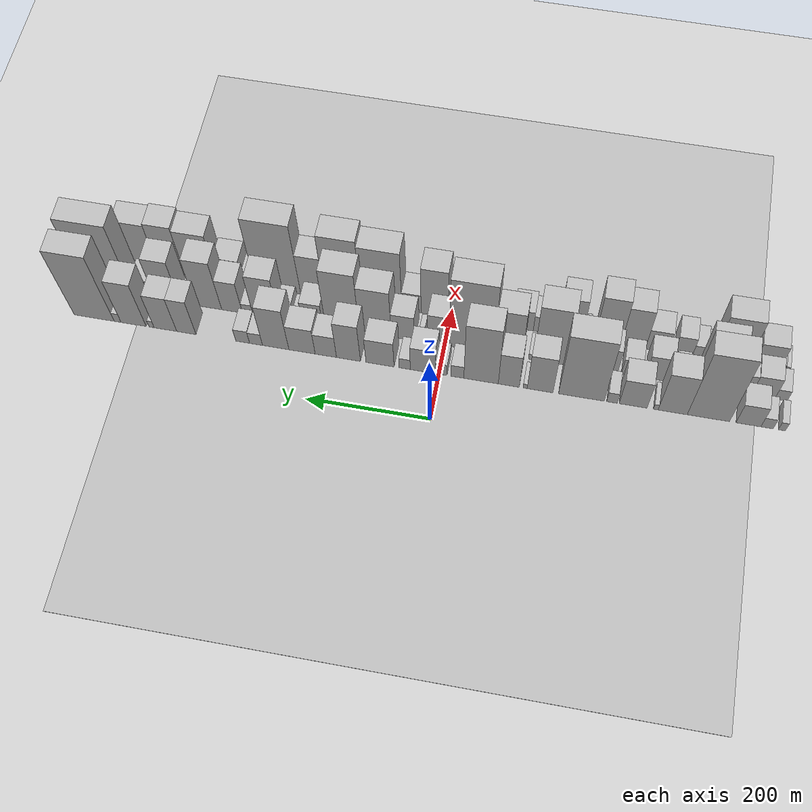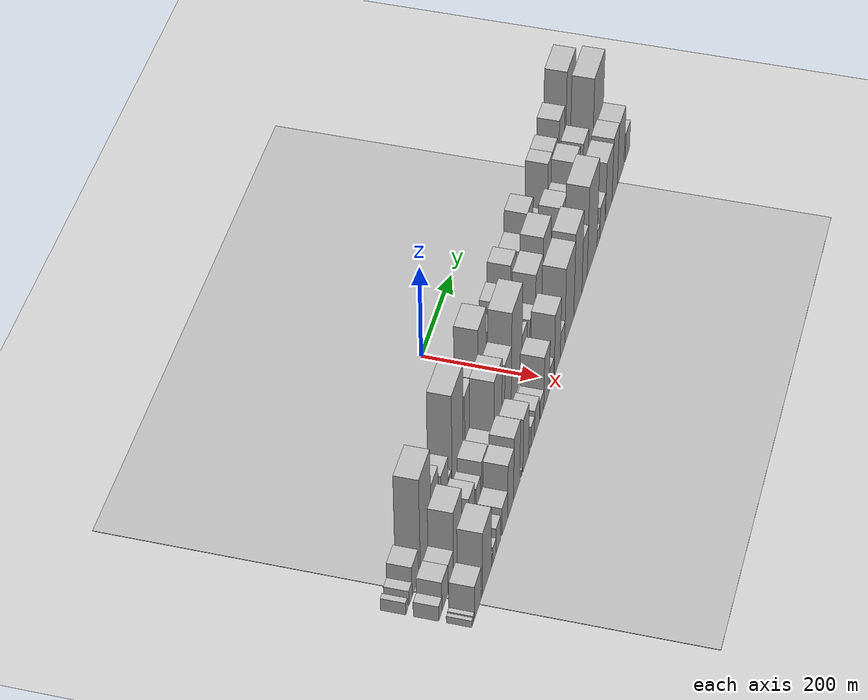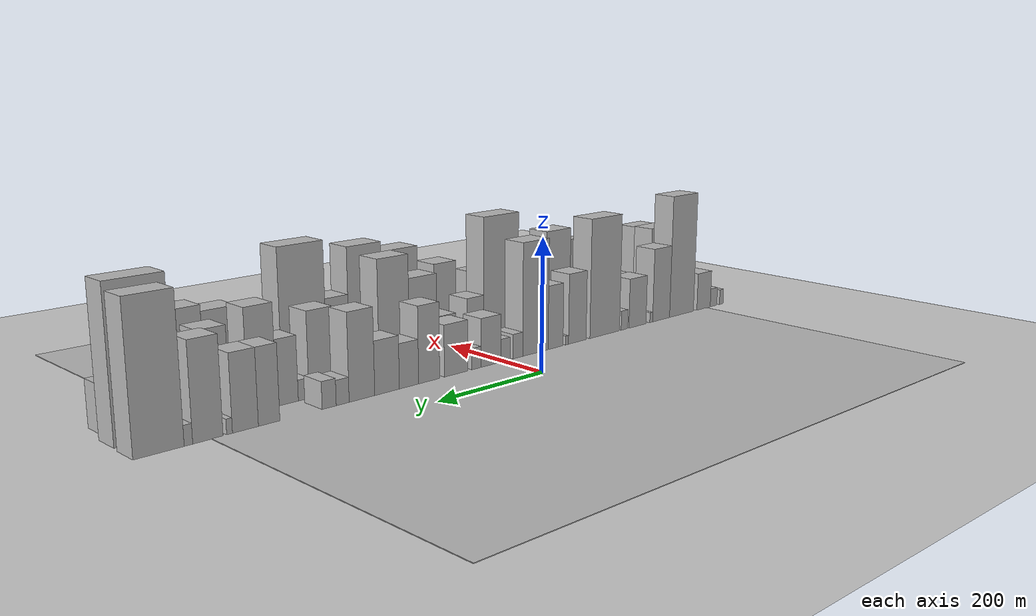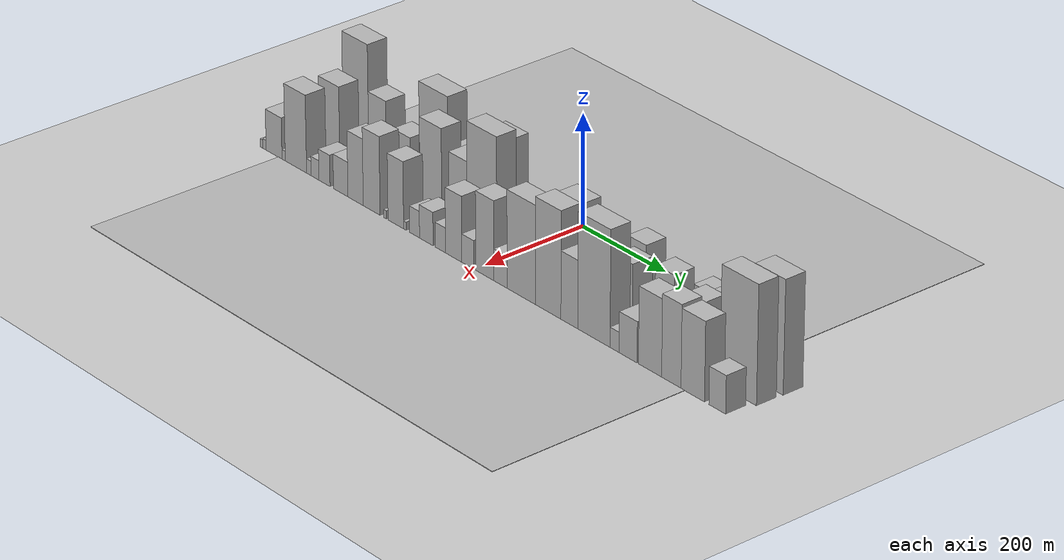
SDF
<?xml version="1.0" encoding="utf-8"?>

<sdf version="1.6">

   <world name="default">

      <gui fullscreen="0">

         <camera name="user_camera">

            <pose>-15 0 4.57585 0 0 0</pose>

            <view_controller>orbit</view_controller>

         </camera>

      </gui>

      <scene>

         <sky>

           <clouds>

             <speed>12</speed>

           </clouds>

         </sky>

         <ambient>0.4 0.4 0.4 1</ambient>

         <background>0.7 0.7 0.7 1</background>

         <shadows>1</shadows>

      </scene>

      <gravity>0 0 -9.8066</gravity>

      <magnetic_field>6e-06 2.3e-05 -4.2e-05</magnetic_field>

      <physics default="0" name="default_physics" type="ode">

         <ode>

            <solver>

               <type>quick</type>

               <iters>10</iters>

               <sor>1.0</sor>

               <use_dynamic_moi_rescaling>0</use_dynamic_moi_rescaling>

            </solver>

            <constraints>

               <cfm>0</cfm>

               <erp>0.2</erp>

               <contact_max_correcting_vel>100</contact_max_correcting_vel>

               <contact_surface_layer>0.001</contact_surface_layer>

            </constraints>

         </ode>

         <max_step_size>0.004</max_step_size>

         <real_time_factor>1</real_time_factor>

         <real_time_update_rate>250</real_time_update_rate>

      </physics>

      <light name="sun" type="directional">

         <cast_shadows>1</cast_shadows>

         <pose>0 0 10 0 0 0</pose>

         <diffuse>0.8 0.8 0.8 1</diffuse>

         <specular>0.2 0.2 0.2 1</specular>

         <attenuation>

            <range>1000</range>

            <constant>0.9</constant>

            <linear>0.01</linear>

            <quadratic>0.001</quadratic>

         </attenuation>

         <direction>-0.5 0.1 -0.9</direction>

      </light>

      <include>

         <name>ground_plane_1</name>

         <uri>model://HANNAS_ground_plane</uri>

         <pose>0 0 0  0 0 0</pose>

      </include>

      <include>

         <name>ground_plane_2</name>

         <uri>model://HANNAS_ground_plane</uri>

         <pose>100 0 0  0 0 0</pose>

      </include>

      <model name="building_1">

         <static>1</static>

         <pose frame="">100.0000 -542.5164 0 0.000000 0.000000 0.000000</pose>

         <link name="link">

            <pose frame="">0 0 13.50 0 0 0</pose>

            <collision name="collision">

               <geometry>

                  <box>

                     <size>40.0000 10.9673 27.0000</size>

                  </box>

               </geometry>

               <max_contacts>10</max_contacts>

               <surface>

                  <contact>

                     <ode/>

                  </contact>

                  <bounce/>

                  <friction>

                     <torsional>

                        <ode/>

                     </torsional>

                     <ode/>

                  </friction>

               </surface>

            </collision>

            <visual name="visual">

               <cast_shadows>0</cast_shadows>

               <geometry>

                  <box>

                     <size>40.0000 10.9673 27.0000</size>

                  </box>

               </geometry>

               <material>

                  <script>

                     <uri>model://HANNAS_wall/materials/scripts</uri>

                     <uri>model://HANNAS_wall/materials/textures</uri>

                     <name>vrc/HANNAS_wall</name>

                  </script>

               </material>

            </visual>

            <self_collide>0</self_collide>

            <enable_wind>0</enable_wind>

            <kinematic>0</kinematic>

         </link>

      </model>

      <model name="building_2">

         <static>1</static>

         <pose frame="">100.0000 -519.4417 0 0.000000 0.000000 0.000000</pose>

         <link name="link">

            <pose frame="">0 0 16.50 0 0 0</pose>

            <collision name="collision">

               <geometry>

                  <box>

                     <size>40.0000 19.1822 33.0000</size>

                  </box>

               </geometry>

               <max_contacts>10</max_contacts>

               <surface>

                  <contact>

                     <ode/>

                  </contact>

                  <bounce/>

                  <friction>

                     <torsional>

                        <ode/>

                     </torsional>

                     <ode/>

                  </friction>

               </surface>

            </collision>

            <visual name="visual">

               <cast_shadows>0</cast_shadows>

               <geometry>

                  <box>

                     <size>40.0000 19.1822 33.0000</size>

                  </box>

               </geometry>

               <material>

                  <script>

                     <uri>model://HANNAS_wall/materials/scripts</uri>

                     <uri>model://HANNAS_wall/materials/textures</uri>

                     <name>vrc/HANNAS_wall</name>

                  </script>

               </material>

            </visual>

            <self_collide>0</self_collide>

            <enable_wind>0</enable_wind>

            <kinematic>0</kinematic>

         </link>

      </model>

      <model name="building_3">

         <static>1</static>

         <pose frame="">100.0000 -490.4910 0 0.000000 0.000000 0.000000</pose>

         <link name="link">

            <pose frame="">0 0 33.00 0 0 0</pose>

            <collision name="collision">

               <geometry>

                  <box>

                     <size>40.0000 38.7191 66.0000</size>

                  </box>

               </geometry>

               <max_contacts>10</max_contacts>

               <surface>

                  <contact>

                     <ode/>

                  </contact>

                  <bounce/>

                  <friction>

                     <torsional>

                        <ode/>

                     </torsional>

                     <ode/>

                  </friction>

               </surface>

            </collision>

            <visual name="visual">

               <cast_shadows>0</cast_shadows>

               <geometry>

                  <box>

                     <size>40.0000 38.7191 66.0000</size>

                  </box>

               </geometry>

               <material>

                  <script>

                     <uri>model://HANNAS_wall/materials/scripts</uri>

                     <uri>model://HANNAS_wall/materials/textures</uri>

                     <name>vrc/HANNAS_wall</name>

                  </script>

               </material>

            </visual>

            <self_collide>0</self_collide>

            <enable_wind>0</enable_wind>

            <kinematic>0</kinematic>

         </link>

      </model>

      <model name="building_4">

         <static>1</static>

         <pose frame="">100.0000 -427.9888 0 0.000000 0.000000 0.000000</pose>

         <link name="link">

            <pose frame="">0 0 105.00 0 0 0</pose>

            <collision name="collision">

               <geometry>

                  <box>

                     <size>40.0000 66.2853 210.0000</size>

                  </box>

               </geometry>

               <max_contacts>10</max_contacts>

               <surface>

                  <contact>

                     <ode/>

                  </contact>

                  <bounce/>

                  <friction>

                     <torsional>

                        <ode/>

                     </torsional>

                     <ode/>

                  </friction>

               </surface>

            </collision>

            <visual name="visual">

               <cast_shadows>0</cast_shadows>

               <geometry>

                  <box>

                     <size>40.0000 66.2853 210.0000</size>

                  </box>

               </geometry>

               <material>

                  <script>

                     <uri>model://HANNAS_wall/materials/scripts</uri>

                     <uri>model://HANNAS_wall/materials/textures</uri>

                     <name>vrc/HANNAS_wall</name>

                  </script>

               </material>

            </visual>

            <self_collide>0</self_collide>

            <enable_wind>0</enable_wind>

            <kinematic>0</kinematic>

         </link>

      </model>

      <model name="building_5">

         <static>1</static>

         <pose frame="">100.0000 -371.9777 0 0.000000 0.000000 0.000000</pose>

         <link name="link">

            <pose frame="">0 0 63.00 0 0 0</pose>

            <collision name="collision">

               <geometry>

                  <box>

                     <size>40.0000 45.7369 126.0000</size>

                  </box>

               </geometry>

               <max_contacts>10</max_contacts>

               <surface>

                  <contact>

                     <ode/>

                  </contact>

                  <bounce/>

                  <friction>

                     <torsional>

                        <ode/>

                     </torsional>

                     <ode/>

                  </friction>

               </surface>

            </collision>

            <visual name="visual">

               <cast_shadows>0</cast_shadows>

               <geometry>

                  <box>

                     <size>40.0000 45.7369 126.0000</size>

                  </box>

               </geometry>

               <material>

                  <script>

                     <uri>model://HANNAS_wall/materials/scripts</uri>

                     <uri>model://HANNAS_wall/materials/textures</uri>

                     <name>vrc/HANNAS_wall</name>

                  </script>

               </material>

            </visual>

            <self_collide>0</self_collide>

            <enable_wind>0</enable_wind>

            <kinematic>0</kinematic>

         </link>

      </model>

      <model name="building_6">

         <static>1</static>

         <pose frame="">100.0000 -345.3822 0 0.000000 0.000000 0.000000</pose>

         <link name="link">

            <pose frame="">0 0 9.00 0 0 0</pose>

            <collision name="collision">

               <geometry>

                  <box>

                     <size>40.0000 7.4540 18.0000</size>

                  </box>

               </geometry>

               <max_contacts>10</max_contacts>

               <surface>

                  <contact>

                     <ode/>

                  </contact>

                  <bounce/>

                  <friction>

                     <torsional>

                        <ode/>

                     </torsional>

                     <ode/>

                  </friction>

               </surface>

            </collision>

            <visual name="visual">

               <cast_shadows>0</cast_shadows>

               <geometry>

                  <box>

                     <size>40.0000 7.4540 18.0000</size>

                  </box>

               </geometry>

               <material>

                  <script>

                     <uri>model://HANNAS_wall/materials/scripts</uri>

                     <uri>model://HANNAS_wall/materials/textures</uri>

                     <name>vrc/HANNAS_wall</name>

                  </script>

               </material>

            </visual>

            <self_collide>0</self_collide>

            <enable_wind>0</enable_wind>

            <kinematic>0</kinematic>

         </link>

      </model>

      <model name="building_7">

         <static>1</static>

         <pose frame="">100.0000 -309.6025 0 0.000000 0.000000 0.000000</pose>

         <link name="link">

            <pose frame="">0 0 42.00 0 0 0</pose>

            <collision name="collision">

               <geometry>

                  <box>

                     <size>40.0000 44.1054 84.0000</size>

                  </box>

               </geometry>

               <max_contacts>10</max_contacts>

               <surface>

                  <contact>

                     <ode/>

                  </contact>

                  <bounce/>

                  <friction>

                     <torsional>

                        <ode/>

                     </torsional>

                     <ode/>

                  </friction>

               </surface>

            </collision>

            <visual name="visual">

               <cast_shadows>0</cast_shadows>

               <geometry>

                  <box>

                     <size>40.0000 44.1054 84.0000</size>

                  </box>

               </geometry>

               <material>

                  <script>

                     <uri>model://HANNAS_wall/materials/scripts</uri>

                     <uri>model://HANNAS_wall/materials/textures</uri>

                     <name>vrc/HANNAS_wall</name>

                  </script>

               </material>

            </visual>

            <self_collide>0</self_collide>

            <enable_wind>0</enable_wind>

            <kinematic>0</kinematic>

         </link>

      </model>

      <model name="building_8">

         <static>1</static>

         <pose frame="">100.0000 -276.2103 0 0.000000 0.000000 0.000000</pose>

         <link name="link">

            <pose frame="">0 0 16.50 0 0 0</pose>

            <collision name="collision">

               <geometry>

                  <box>

                     <size>40.0000 16.6790 33.0000</size>

                  </box>

               </geometry>

               <max_contacts>10</max_contacts>

               <surface>

                  <contact>

                     <ode/>

                  </contact>

                  <bounce/>

                  <friction>

                     <torsional>

                        <ode/>

                     </torsional>

                     <ode/>

                  </friction>

               </surface>

            </collision>

            <visual name="visual">

               <cast_shadows>0</cast_shadows>

               <geometry>

                  <box>

                     <size>40.0000 16.6790 33.0000</size>

                  </box>

               </geometry>

               <material>

                  <script>

                     <uri>model://HANNAS_wall/materials/scripts</uri>

                     <uri>model://HANNAS_wall/materials/textures</uri>

                     <name>vrc/HANNAS_wall</name>

                  </script>

               </material>

            </visual>

            <self_collide>0</self_collide>

            <enable_wind>0</enable_wind>

            <kinematic>0</kinematic>

         </link>

      </model>

      <model name="building_9">

         <static>1</static>

         <pose frame="">100.0000 -227.6082 0 0.000000 0.000000 0.000000</pose>

         <link name="link">

            <pose frame="">0 0 97.50 0 0 0</pose>

            <collision name="collision">

               <geometry>

                  <box>

                     <size>40.0000 72.5251 195.0000</size>

                  </box>

               </geometry>

               <max_contacts>10</max_contacts>

               <surface>

                  <contact>

                     <ode/>

                  </contact>

                  <bounce/>

                  <friction>

                     <torsional>

                        <ode/>

                     </torsional>

                     <ode/>

                  </friction>

               </surface>

            </collision>

            <visual name="visual">

               <cast_shadows>0</cast_shadows>

               <geometry>

                  <box>

                     <size>40.0000 72.5251 195.0000</size>

                  </box>

               </geometry>

               <material>

                  <script>

                     <uri>model://HANNAS_wall/materials/scripts</uri>

                     <uri>model://HANNAS_wall/materials/textures</uri>

                     <name>vrc/HANNAS_wall</name>

                  </script>

               </material>

            </visual>

            <self_collide>0</self_collide>

            <enable_wind>0</enable_wind>

            <kinematic>0</kinematic>

         </link>

      </model>

      <model name="building_10">

         <static>1</static>

         <pose frame="">100.0000 -161.7395 0 0.000000 0.000000 0.000000</pose>

         <link name="link">

            <pose frame="">0 0 57.00 0 0 0</pose>

            <collision name="collision">

               <geometry>

                  <box>

                     <size>40.0000 41.2122 114.0000</size>

                  </box>

               </geometry>

               <max_contacts>10</max_contacts>

               <surface>

                  <contact>

                     <ode/>

                  </contact>

                  <bounce/>

                  <friction>

                     <torsional>

                        <ode/>

                     </torsional>

                     <ode/>

                  </friction>

               </surface>

            </collision>

            <visual name="visual">

               <cast_shadows>0</cast_shadows>

               <geometry>

                  <box>

                     <size>40.0000 41.2122 114.0000</size>

                  </box>

               </geometry>

               <material>

                  <script>

                     <uri>model://HANNAS_wall/materials/scripts</uri>

                     <uri>model://HANNAS_wall/materials/textures</uri>

                     <name>vrc/HANNAS_wall</name>

                  </script>

               </material>

            </visual>

            <self_collide>0</self_collide>

            <enable_wind>0</enable_wind>

            <kinematic>0</kinematic>

         </link>

      </model>

      <model name="building_11">

         <static>1</static>

         <pose frame="">100.0000 -137.8704 0 0.000000 0.000000 0.000000</pose>

         <link name="link">

            <pose frame="">0 0 7.50 0 0 0</pose>

            <collision name="collision">

               <geometry>

                  <box>

                     <size>40.0000 6.5261 15.0000</size>

                  </box>

               </geometry>

               <max_contacts>10</max_contacts>

               <surface>

                  <contact>

                     <ode/>

                  </contact>

                  <bounce/>

                  <friction>

                     <torsional>

                        <ode/>

                     </torsional>

                     <ode/>

                  </friction>

               </surface>

            </collision>

            <visual name="visual">

               <cast_shadows>0</cast_shadows>

               <geometry>

                  <box>

                     <size>40.0000 6.5261 15.0000</size>

                  </box>

               </geometry>

               <material>

                  <script>

                     <uri>model://HANNAS_wall/materials/scripts</uri>

                     <uri>model://HANNAS_wall/materials/textures</uri>

                     <name>vrc/HANNAS_wall</name>

                  </script>

               </material>

            </visual>

            <self_collide>0</self_collide>

            <enable_wind>0</enable_wind>

            <kinematic>0</kinematic>

         </link>

      </model>

      <model name="building_12">

         <static>1</static>

         <pose frame="">100.0000 -111.7329 0 0.000000 0.000000 0.000000</pose>

         <link name="link">

            <pose frame="">0 0 51.00 0 0 0</pose>

            <collision name="collision">

               <geometry>

                  <box>

                     <size>40.0000 33.7489 102.0000</size>

                  </box>

               </geometry>

               <max_contacts>10</max_contacts>

               <surface>

                  <contact>

                     <ode/>

                  </contact>

                  <bounce/>

                  <friction>

                     <torsional>

                        <ode/>

                     </torsional>

                     <ode/>

                  </friction>

               </surface>

            </collision>

            <visual name="visual">

               <cast_shadows>0</cast_shadows>

               <geometry>

                  <box>

                     <size>40.0000 33.7489 102.0000</size>

                  </box>

               </geometry>

               <material>

                  <script>

                     <uri>model://HANNAS_wall/materials/scripts</uri>

                     <uri>model://HANNAS_wall/materials/textures</uri>

                     <name>vrc/HANNAS_wall</name>

                  </script>

               </material>

            </visual>

            <self_collide>0</self_collide>

            <enable_wind>0</enable_wind>

            <kinematic>0</kinematic>

         </link>

      </model>

      <model name="building_13">

         <static>1</static>

         <pose frame="">100.0000 -67.0832 0 0.000000 0.000000 0.000000</pose>

         <link name="link">

            <pose frame="">0 0 88.50 0 0 0</pose>

            <collision name="collision">

               <geometry>

                  <box>

                     <size>40.0000 55.5505 177.0000</size>

                  </box>

               </geometry>

               <max_contacts>10</max_contacts>

               <surface>

                  <contact>

                     <ode/>

                  </contact>

                  <bounce/>

                  <friction>

                     <torsional>

                        <ode/>

                     </torsional>

                     <ode/>

                  </friction>

               </surface>

            </collision>

            <visual name="visual">

               <cast_shadows>0</cast_shadows>

               <geometry>

                  <box>

                     <size>40.0000 55.5505 177.0000</size>

                  </box>

               </geometry>

               <material>

                  <script>

                     <uri>model://HANNAS_wall/materials/scripts</uri>

                     <uri>model://HANNAS_wall/materials/textures</uri>

                     <name>vrc/HANNAS_wall</name>

                  </script>

               </material>

            </visual>

            <self_collide>0</self_collide>

            <enable_wind>0</enable_wind>

            <kinematic>0</kinematic>

         </link>

      </model>

      <model name="building_14">

         <static>1</static>

         <pose frame="">100.0000 -28.7633 0 0.000000 0.000000 0.000000</pose>

         <link name="link">

            <pose frame="">0 0 19.50 0 0 0</pose>

            <collision name="collision">

               <geometry>

                  <box>

                     <size>40.0000 21.0894 39.0000</size>

                  </box>

               </geometry>

               <max_contacts>10</max_contacts>

               <surface>

                  <contact>

                     <ode/>

                  </contact>

                  <bounce/>

                  <friction>

                     <torsional>

                        <ode/>

                     </torsional>

                     <ode/>

                  </friction>

               </surface>

            </collision>

            <visual name="visual">

               <cast_shadows>0</cast_shadows>

               <geometry>

                  <box>

                     <size>40.0000 21.0894 39.0000</size>

                  </box>

               </geometry>

               <material>

                  <script>

                     <uri>model://HANNAS_wall/materials/scripts</uri>

                     <uri>model://HANNAS_wall/materials/textures</uri>

                     <name>vrc/HANNAS_wall</name>

                  </script>

               </material>

            </visual>

            <self_collide>0</self_collide>

            <enable_wind>0</enable_wind>

            <kinematic>0</kinematic>

         </link>

      </model>

      <model name="building_15">

         <static>1</static>

         <pose frame="">100.0000 -2.6268 0 0.000000 0.000000 0.000000</pose>

         <link name="link">

            <pose frame="">0 0 18.00 0 0 0</pose>

            <collision name="collision">

               <geometry>

                  <box>

                     <size>40.0000 19.1836 36.0000</size>

                  </box>

               </geometry>

               <max_contacts>10</max_contacts>

               <surface>

                  <contact>

                     <ode/>

                  </contact>

                  <bounce/>

                  <friction>

                     <torsional>

                        <ode/>

                     </torsional>

                     <ode/>

                  </friction>

               </surface>

            </collision>

            <visual name="visual">

               <cast_shadows>0</cast_shadows>

               <geometry>

                  <box>

                     <size>40.0000 19.1836 36.0000</size>

                  </box>

               </geometry>

               <material>

                  <script>

                     <uri>model://HANNAS_wall/materials/scripts</uri>

                     <uri>model://HANNAS_wall/materials/textures</uri>

                     <name>vrc/HANNAS_wall</name>

                  </script>

               </material>

            </visual>

            <self_collide>0</self_collide>

            <enable_wind>0</enable_wind>

            <kinematic>0</kinematic>

         </link>

      </model>

      <model name="building_16">

         <static>1</static>

         <pose frame="">100.0000 27.1155 0 0.000000 0.000000 0.000000</pose>

         <link name="link">

            <pose frame="">0 0 37.50 0 0 0</pose>

            <collision name="collision">

               <geometry>

                  <box>

                     <size>40.0000 40.3009 75.0000</size>

                  </box>

               </geometry>

               <max_contacts>10</max_contacts>

               <surface>

                  <contact>

                     <ode/>

                  </contact>

                  <bounce/>

                  <friction>

                     <torsional>

                        <ode/>

                     </torsional>

                     <ode/>

                  </friction>

               </surface>

            </collision>

            <visual name="visual">

               <cast_shadows>0</cast_shadows>

               <geometry>

                  <box>

                     <size>40.0000 40.3009 75.0000</size>

                  </box>

               </geometry>

               <material>

                  <script>

                     <uri>model://HANNAS_wall/materials/scripts</uri>

                     <uri>model://HANNAS_wall/materials/textures</uri>

                     <name>vrc/HANNAS_wall</name>

                  </script>

               </material>

            </visual>

            <self_collide>0</self_collide>

            <enable_wind>0</enable_wind>

            <kinematic>0</kinematic>

         </link>

      </model>

      <model name="building_17">

         <static>1</static>

         <pose frame="">100.0000 56.4438 0 0.000000 0.000000 0.000000</pose>

         <link name="link">

            <pose frame="">0 0 16.50 0 0 0</pose>

            <collision name="collision">

               <geometry>

                  <box>

                     <size>40.0000 18.3558 33.0000</size>

                  </box>

               </geometry>

               <max_contacts>10</max_contacts>

               <surface>

                  <contact>

                     <ode/>

                  </contact>

                  <bounce/>

                  <friction>

                     <torsional>

                        <ode/>

                     </torsional>

                     <ode/>

                  </friction>

               </surface>

            </collision>

            <visual name="visual">

               <cast_shadows>0</cast_shadows>

               <geometry>

                  <box>

                     <size>40.0000 18.3558 33.0000</size>

                  </box>

               </geometry>

               <material>

                  <script>

                     <uri>model://HANNAS_wall/materials/scripts</uri>

                     <uri>model://HANNAS_wall/materials/textures</uri>

                     <name>vrc/HANNAS_wall</name>

                  </script>

               </material>

            </visual>

            <self_collide>0</self_collide>

            <enable_wind>0</enable_wind>

            <kinematic>0</kinematic>

         </link>

      </model>

      <model name="building_18">

         <static>1</static>

         <pose frame="">100.0000 96.5650 0 0.000000 0.000000 0.000000</pose>

         <link name="link">

            <pose frame="">0 0 39.00 0 0 0</pose>

            <collision name="collision">

               <geometry>

                  <box>

                     <size>40.0000 45.8865 78.0000</size>

                  </box>

               </geometry>

               <max_contacts>10</max_contacts>

               <surface>

                  <contact>

                     <ode/>

                  </contact>

                  <bounce/>

                  <friction>

                     <torsional>

                        <ode/>

                     </torsional>

                     <ode/>

                  </friction>

               </surface>

            </collision>

            <visual name="visual">

               <cast_shadows>0</cast_shadows>

               <geometry>

                  <box>

                     <size>40.0000 45.8865 78.0000</size>

                  </box>

               </geometry>

               <material>

                  <script>

                     <uri>model://HANNAS_wall/materials/scripts</uri>

                     <uri>model://HANNAS_wall/materials/textures</uri>

                     <name>vrc/HANNAS_wall</name>

                  </script>

               </material>

            </visual>

            <self_collide>0</self_collide>

            <enable_wind>0</enable_wind>

            <kinematic>0</kinematic>

         </link>

      </model>

      <model name="building_19">

         <static>1</static>

         <pose frame="">100.0000 148.1365 0 0.000000 0.000000 0.000000</pose>

         <link name="link">

            <pose frame="">0 0 57.00 0 0 0</pose>

            <collision name="collision">

               <geometry>

                  <box>

                     <size>40.0000 39.2566 114.0000</size>

                  </box>

               </geometry>

               <max_contacts>10</max_contacts>

               <surface>

                  <contact>

                     <ode/>

                  </contact>

                  <bounce/>

                  <friction>

                     <torsional>

                        <ode/>

                     </torsional>

                     <ode/>

                  </friction>

               </surface>

            </collision>

            <visual name="visual">

               <cast_shadows>0</cast_shadows>

               <geometry>

                  <box>

                     <size>40.0000 39.2566 114.0000</size>

                  </box>

               </geometry>

               <material>

                  <script>

                     <uri>model://HANNAS_wall/materials/scripts</uri>

                     <uri>model://HANNAS_wall/materials/textures</uri>

                     <name>vrc/HANNAS_wall</name>

                  </script>

               </material>

            </visual>

            <self_collide>0</self_collide>

            <enable_wind>0</enable_wind>

            <kinematic>0</kinematic>

         </link>

      </model>

      <model name="building_20">

         <static>1</static>

         <pose frame="">100.0000 185.2685 0 0.000000 0.000000 0.000000</pose>

         <link name="link">

            <pose frame="">0 0 33.00 0 0 0</pose>

            <collision name="collision">

               <geometry>

                  <box>

                     <size>40.0000 35.0073 66.0000</size>

                  </box>

               </geometry>

               <max_contacts>10</max_contacts>

               <surface>

                  <contact>

                     <ode/>

                  </contact>

                  <bounce/>

                  <friction>

                     <torsional>

                        <ode/>

                     </torsional>

                     <ode/>

                  </friction>

               </surface>

            </collision>

            <visual name="visual">

               <cast_shadows>0</cast_shadows>

               <geometry>

                  <box>

                     <size>40.0000 35.0073 66.0000</size>

                  </box>

               </geometry>

               <material>

                  <script>

                     <uri>model://HANNAS_wall/materials/scripts</uri>

                     <uri>model://HANNAS_wall/materials/textures</uri>

                     <name>vrc/HANNAS_wall</name>

                  </script>

               </material>

            </visual>

            <self_collide>0</self_collide>

            <enable_wind>0</enable_wind>

            <kinematic>0</kinematic>

         </link>

      </model>

      <model name="building_21">

         <static>1</static>

         <pose frame="">100.0000 224.4527 0 0.000000 0.000000 0.000000</pose>

         <link name="link">

            <pose frame="">0 0 39.00 0 0 0</pose>

            <collision name="collision">

               <geometry>

                  <box>

                     <size>40.0000 43.3611 78.0000</size>

                  </box>

               </geometry>

               <max_contacts>10</max_contacts>

               <surface>

                  <contact>

                     <ode/>

                  </contact>

                  <bounce/>

                  <friction>

                     <torsional>

                        <ode/>

                     </torsional>

                     <ode/>

                  </friction>

               </surface>

            </collision>

            <visual name="visual">

               <cast_shadows>0</cast_shadows>

               <geometry>

                  <box>

                     <size>40.0000 43.3611 78.0000</size>

                  </box>

               </geometry>

               <material>

                  <script>

                     <uri>model://HANNAS_wall/materials/scripts</uri>

                     <uri>model://HANNAS_wall/materials/textures</uri>

                     <name>vrc/HANNAS_wall</name>

                  </script>

               </material>

            </visual>

            <self_collide>0</self_collide>

            <enable_wind>0</enable_wind>

            <kinematic>0</kinematic>

         </link>

      </model>

      <model name="building_22">

         <static>1</static>

         <pose frame="">100.0000 267.9557 0 0.000000 0.000000 0.000000</pose>

         <link name="link">

            <pose frame="">0 0 63.00 0 0 0</pose>

            <collision name="collision">

               <geometry>

                  <box>

                     <size>40.0000 43.6451 126.0000</size>

                  </box>

               </geometry>

               <max_contacts>10</max_contacts>

               <surface>

                  <contact>

                     <ode/>

                  </contact>

                  <bounce/>

                  <friction>

                     <torsional>

                        <ode/>

                     </torsional>

                     <ode/>

                  </friction>

               </surface>

            </collision>

            <visual name="visual">

               <cast_shadows>0</cast_shadows>

               <geometry>

                  <box>

                     <size>40.0000 43.6451 126.0000</size>

                  </box>

               </geometry>

               <material>

                  <script>

                     <uri>model://HANNAS_wall/materials/scripts</uri>

                     <uri>model://HANNAS_wall/materials/textures</uri>

                     <name>vrc/HANNAS_wall</name>

                  </script>

               </material>

            </visual>

            <self_collide>0</self_collide>

            <enable_wind>0</enable_wind>

            <kinematic>0</kinematic>

         </link>

      </model>

      <model name="building_23">

         <static>1</static>

         <pose frame="">100.0000 300.5000 0 0.000000 0.000000 0.000000</pose>

         <link name="link">

            <pose frame="">0 0 18.00 0 0 0</pose>

            <collision name="collision">

               <geometry>

                  <box>

                     <size>40.0000 21.4434 36.0000</size>

                  </box>

               </geometry>

               <max_contacts>10</max_contacts>

               <surface>

                  <contact>

                     <ode/>

                  </contact>

                  <bounce/>

                  <friction>

                     <torsional>

                        <ode/>

                     </torsional>

                     <ode/>

                  </friction>

               </surface>

            </collision>

            <visual name="visual">

               <cast_shadows>0</cast_shadows>

               <geometry>

                  <box>

                     <size>40.0000 21.4434 36.0000</size>

                  </box>

               </geometry>

               <material>

                  <script>

                     <uri>model://HANNAS_wall/materials/scripts</uri>

                     <uri>model://HANNAS_wall/materials/textures</uri>

                     <name>vrc/HANNAS_wall</name>

                  </script>

               </material>

            </visual>

            <self_collide>0</self_collide>

            <enable_wind>0</enable_wind>

            <kinematic>0</kinematic>

         </link>

      </model>

      <model name="building_24">

         <static>1</static>

         <pose frame="">100.0000 322.6901 0 0.000000 0.000000 0.000000</pose>

         <link name="link">

            <pose frame="">0 0 19.50 0 0 0</pose>

            <collision name="collision">

               <geometry>

                  <box>

                     <size>40.0000 22.9368 39.0000</size>

                  </box>

               </geometry>

               <max_contacts>10</max_contacts>

               <surface>

                  <contact>

                     <ode/>

                  </contact>

                  <bounce/>

                  <friction>

                     <torsional>

                        <ode/>

                     </torsional>

                     <ode/>

                  </friction>

               </surface>

            </collision>

            <visual name="visual">

               <cast_shadows>0</cast_shadows>

               <geometry>

                  <box>

                     <size>40.0000 22.9368 39.0000</size>

                  </box>

               </geometry>

               <material>

                  <script>

                     <uri>model://HANNAS_wall/materials/scripts</uri>

                     <uri>model://HANNAS_wall/materials/textures</uri>

                     <name>vrc/HANNAS_wall</name>

                  </script>

               </material>

            </visual>

            <self_collide>0</self_collide>

            <enable_wind>0</enable_wind>

            <kinematic>0</kinematic>

         </link>

      </model>

      <model name="building_25">

         <static>1</static>

         <pose frame="">100.0000 416.6249 0 0.000000 0.000000 0.000000</pose>

         <link name="link">

            <pose frame="">0 0 52.50 0 0 0</pose>

            <collision name="collision">

               <geometry>

                  <box>

                     <size>40.0000 32.3110 105.0000</size>

                  </box>

               </geometry>

               <max_contacts>10</max_contacts>

               <surface>

                  <contact>

                     <ode/>

                  </contact>

                  <bounce/>

                  <friction>

                     <torsional>

                        <ode/>

                     </torsional>

                     <ode/>

                  </friction>

               </surface>

            </collision>

            <visual name="visual">

               <cast_shadows>0</cast_shadows>

               <geometry>

                  <box>

                     <size>40.0000 32.3110 105.0000</size>

                  </box>

               </geometry>

               <material>

                  <script>

                     <uri>model://HANNAS_wall/materials/scripts</uri>

                     <uri>model://HANNAS_wall/materials/textures</uri>

                     <name>vrc/HANNAS_wall</name>

                  </script>

               </material>

            </visual>

            <self_collide>0</self_collide>

            <enable_wind>0</enable_wind>

            <kinematic>0</kinematic>

         </link>

      </model>

      <model name="building_26">

         <static>1</static>

         <pose frame="">100.0000 451.7565 0 0.000000 0.000000 0.000000</pose>

         <link name="link">

            <pose frame="">0 0 52.50 0 0 0</pose>

            <collision name="collision">

               <geometry>

                  <box>

                     <size>40.0000 37.9522 105.0000</size>

                  </box>

               </geometry>

               <max_contacts>10</max_contacts>

               <surface>

                  <contact>

                     <ode/>

                  </contact>

                  <bounce/>

                  <friction>

                     <torsional>

                        <ode/>

                     </torsional>

                     <ode/>

                  </friction>

               </surface>

            </collision>

            <visual name="visual">

               <cast_shadows>0</cast_shadows>

               <geometry>

                  <box>

                     <size>40.0000 37.9522 105.0000</size>

                  </box>

               </geometry>

               <material>

                  <script>

                     <uri>model://HANNAS_wall/materials/scripts</uri>

                     <uri>model://HANNAS_wall/materials/textures</uri>

                     <name>vrc/HANNAS_wall</name>

                  </script>

               </material>

            </visual>

            <self_collide>0</self_collide>

            <enable_wind>0</enable_wind>

            <kinematic>0</kinematic>

         </link>

      </model>

      <model name="building_27">

         <static>1</static>

         <pose frame="">100.0000 474.9390 0 0.000000 0.000000 0.000000</pose>

         <link name="link">

            <pose frame="">0 0 10.50 0 0 0</pose>

            <collision name="collision">

               <geometry>

                  <box>

                     <size>40.0000 8.4129 21.0000</size>

                  </box>

               </geometry>

               <max_contacts>10</max_contacts>

               <surface>

                  <contact>

                     <ode/>

                  </contact>

                  <bounce/>

                  <friction>

                     <torsional>

                        <ode/>

                     </torsional>

                     <ode/>

                  </friction>

               </surface>

            </collision>

            <visual name="visual">

               <cast_shadows>0</cast_shadows>

               <geometry>

                  <box>

                     <size>40.0000 8.4129 21.0000</size>

                  </box>

               </geometry>

               <material>

                  <script>

                     <uri>model://HANNAS_wall/materials/scripts</uri>

                     <uri>model://HANNAS_wall/materials/textures</uri>

                     <name>vrc/HANNAS_wall</name>

                  </script>

               </material>

            </visual>

            <self_collide>0</self_collide>

            <enable_wind>0</enable_wind>

            <kinematic>0</kinematic>

         </link>

      </model>

      <model name="building_28">

         <static>1</static>

         <pose frame="">100.0000 505.3186 0 0.000000 0.000000 0.000000</pose>

         <link name="link">

            <pose frame="">0 0 66.00 0 0 0</pose>

            <collision name="collision">

               <geometry>

                  <box>

                     <size>40.0000 42.3463 132.0000</size>

                  </box>

               </geometry>

               <max_contacts>10</max_contacts>

               <surface>

                  <contact>

                     <ode/>

                  </contact>

                  <bounce/>

                  <friction>

                     <torsional>

                        <ode/>

                     </torsional>

                     <ode/>

                  </friction>

               </surface>

            </collision>

            <visual name="visual">

               <cast_shadows>0</cast_shadows>

               <geometry>

                  <box>

                     <size>40.0000 42.3463 132.0000</size>

                  </box>

               </geometry>

               <material>

                  <script>

                     <uri>model://HANNAS_wall/materials/scripts</uri>

                     <uri>model://HANNAS_wall/materials/textures</uri>

                     <name>vrc/HANNAS_wall</name>

                  </script>

               </material>

            </visual>

            <self_collide>0</self_collide>

            <enable_wind>0</enable_wind>

            <kinematic>0</kinematic>

         </link>

      </model>

      <model name="building_29">

         <static>1</static>

         <pose frame="">100.0000 532.2817 0 0.000000 0.000000 0.000000</pose>

         <link name="link">

            <pose frame="">0 0 13.50 0 0 0</pose>

            <collision name="collision">

               <geometry>

                  <box>

                     <size>40.0000 11.5799 27.0000</size>

                  </box>

               </geometry>

               <max_contacts>10</max_contacts>

               <surface>

                  <contact>

                     <ode/>

                  </contact>

                  <bounce/>

                  <friction>

                     <torsional>

                        <ode/>

                     </torsional>

                     <ode/>

                  </friction>

               </surface>

            </collision>

            <visual name="visual">

               <cast_shadows>0</cast_shadows>

               <geometry>

                  <box>

                     <size>40.0000 11.5799 27.0000</size>

                  </box>

               </geometry>

               <material>

                  <script>

                     <uri>model://HANNAS_wall/materials/scripts</uri>

                     <uri>model://HANNAS_wall/materials/textures</uri>

                     <name>vrc/HANNAS_wall</name>

                  </script>

               </material>

            </visual>

            <self_collide>0</self_collide>

            <enable_wind>0</enable_wind>

            <kinematic>0</kinematic>

         </link>

      </model>

      <model name="building_30">

         <static>1</static>

         <pose frame="">100.0000 571.8562 0 0.000000 0.000000 0.000000</pose>

         <link name="link">

            <pose frame="">0 0 99.00 0 0 0</pose>

            <collision name="collision">

               <geometry>

                  <box>

                     <size>40.0000 67.5692 198.0000</size>

                  </box>

               </geometry>

               <max_contacts>10</max_contacts>

               <surface>

                  <contact>

                     <ode/>

                  </contact>

                  <bounce/>

                  <friction>

                     <torsional>

                        <ode/>

                     </torsional>

                     <ode/>

                  </friction>

               </surface>

            </collision>

            <visual name="visual">

               <cast_shadows>0</cast_shadows>

               <geometry>

                  <box>

                     <size>40.0000 67.5692 198.0000</size>

                  </box>

               </geometry>

               <material>

                  <script>

                     <uri>model://HANNAS_wall/materials/scripts</uri>

                     <uri>model://HANNAS_wall/materials/textures</uri>

                     <name>vrc/HANNAS_wall</name>

                  </script>

               </material>

            </visual>

            <self_collide>0</self_collide>

            <enable_wind>0</enable_wind>

            <kinematic>0</kinematic>

         </link>

      </model>

      <model name="building_31">

         <static>1</static>

         <pose frame="">152.0000 -538.1309 0 0.000000 0.000000 0.000000</pose>

         <link name="link">

            <pose frame="">0 0 16.50 0 0 0</pose>

            <collision name="collision">

               <geometry>

                  <box>

                     <size>40.0000 19.7381 33.0000</size>

                  </box>

               </geometry>

               <max_contacts>10</max_contacts>

               <surface>

                  <contact>

                     <ode/>

                  </contact>

                  <bounce/>

                  <friction>

                     <torsional>

                        <ode/>

                     </torsional>

                     <ode/>

                  </friction>

               </surface>

            </collision>

            <visual name="visual">

               <cast_shadows>0</cast_shadows>

               <geometry>

                  <box>

                     <size>40.0000 19.7381 33.0000</size>

                  </box>

               </geometry>

               <material>

                  <script>

                     <uri>model://HANNAS_wall/materials/scripts</uri>

                     <uri>model://HANNAS_wall/materials/textures</uri>

                     <name>vrc/HANNAS_wall</name>

                  </script>

               </material>

            </visual>

            <self_collide>0</self_collide>

            <enable_wind>0</enable_wind>

            <kinematic>0</kinematic>

         </link>

      </model>

      <model name="building_32">

         <static>1</static>

         <pose frame="">152.0000 -509.7817 0 0.000000 0.000000 0.000000</pose>

         <link name="link">

            <pose frame="">0 0 33.00 0 0 0</pose>

            <collision name="collision">

               <geometry>

                  <box>

                     <size>40.0000 36.9604 66.0000</size>

                  </box>

               </geometry>

               <max_contacts>10</max_contacts>

               <surface>

                  <contact>

                     <ode/>

                  </contact>

                  <bounce/>

                  <friction>

                     <torsional>

                        <ode/>

                     </torsional>

                     <ode/>

                  </friction>

               </surface>

            </collision>

            <visual name="visual">

               <cast_shadows>0</cast_shadows>

               <geometry>

                  <box>

                     <size>40.0000 36.9604 66.0000</size>

                  </box>

               </geometry>

               <material>

                  <script>

                     <uri>model://HANNAS_wall/materials/scripts</uri>

                     <uri>model://HANNAS_wall/materials/textures</uri>

                     <name>vrc/HANNAS_wall</name>

                  </script>

               </material>

            </visual>

            <self_collide>0</self_collide>

            <enable_wind>0</enable_wind>

            <kinematic>0</kinematic>

         </link>

      </model>

      <model name="building_33">

         <static>1</static>

         <pose frame="">152.0000 -474.4890 0 0.000000 0.000000 0.000000</pose>

         <link name="link">

            <pose frame="">0 0 31.50 0 0 0</pose>

            <collision name="collision">

               <geometry>

                  <box>

                     <size>40.0000 33.6252 63.0000</size>

                  </box>

               </geometry>

               <max_contacts>10</max_contacts>

               <surface>

                  <contact>

                     <ode/>

                  </contact>

                  <bounce/>

                  <friction>

                     <torsional>

                        <ode/>

                     </torsional>

                     <ode/>

                  </friction>

               </surface>

            </collision>

            <visual name="visual">

               <cast_shadows>0</cast_shadows>

               <geometry>

                  <box>

                     <size>40.0000 33.6252 63.0000</size>

                  </box>

               </geometry>

               <material>

                  <script>

                     <uri>model://HANNAS_wall/materials/scripts</uri>

                     <uri>model://HANNAS_wall/materials/textures</uri>

                     <name>vrc/HANNAS_wall</name>

                  </script>

               </material>

            </visual>

            <self_collide>0</self_collide>

            <enable_wind>0</enable_wind>

            <kinematic>0</kinematic>

         </link>

      </model>

      <model name="building_34">

         <static>1</static>

         <pose frame="">152.0000 -431.1492 0 0.000000 0.000000 0.000000</pose>

         <link name="link">

            <pose frame="">0 0 73.50 0 0 0</pose>

            <collision name="collision">

               <geometry>

                  <box>

                     <size>40.0000 53.0543 147.0000</size>

                  </box>

               </geometry>

               <max_contacts>10</max_contacts>

               <surface>

                  <contact>

                     <ode/>

                  </contact>

                  <bounce/>

                  <friction>

                     <torsional>

                        <ode/>

                     </torsional>

                     <ode/>

                  </friction>

               </surface>

            </collision>

            <visual name="visual">

               <cast_shadows>0</cast_shadows>

               <geometry>

                  <box>

                     <size>40.0000 53.0543 147.0000</size>

                  </box>

               </geometry>

               <material>

                  <script>

                     <uri>model://HANNAS_wall/materials/scripts</uri>

                     <uri>model://HANNAS_wall/materials/textures</uri>

                     <name>vrc/HANNAS_wall</name>

                  </script>

               </material>

            </visual>

            <self_collide>0</self_collide>

            <enable_wind>0</enable_wind>

            <kinematic>0</kinematic>

         </link>

      </model>

      <model name="building_35">

         <static>1</static>

         <pose frame="">152.0000 -396.4464 0 0.000000 0.000000 0.000000</pose>

         <link name="link">

            <pose frame="">0 0 15.00 0 0 0</pose>

            <collision name="collision">

               <geometry>

                  <box>

                     <size>40.0000 16.3513 30.0000</size>

                  </box>

               </geometry>

               <max_contacts>10</max_contacts>

               <surface>

                  <contact>

                     <ode/>

                  </contact>

                  <bounce/>

                  <friction>

                     <torsional>

                        <ode/>

                     </torsional>

                     <ode/>

                  </friction>

               </surface>

            </collision>

            <visual name="visual">

               <cast_shadows>0</cast_shadows>

               <geometry>

                  <box>

                     <size>40.0000 16.3513 30.0000</size>

                  </box>

               </geometry>

               <material>

                  <script>

                     <uri>model://HANNAS_wall/materials/scripts</uri>

                     <uri>model://HANNAS_wall/materials/textures</uri>

                     <name>vrc/HANNAS_wall</name>

                  </script>

               </material>

            </visual>

            <self_collide>0</self_collide>

            <enable_wind>0</enable_wind>

            <kinematic>0</kinematic>

         </link>

      </model>

      <model name="building_36">

         <static>1</static>

         <pose frame="">152.0000 -377.8479 0 0.000000 0.000000 0.000000</pose>

         <link name="link">

            <pose frame="">0 0 18.00 0 0 0</pose>

            <collision name="collision">

               <geometry>

                  <box>

                     <size>40.0000 20.8458 36.0000</size>

                  </box>

               </geometry>

               <max_contacts>10</max_contacts>

               <surface>

                  <contact>

                     <ode/>

                  </contact>

                  <bounce/>

                  <friction>

                     <torsional>

                        <ode/>

                     </torsional>

                     <ode/>

                  </friction>

               </surface>

            </collision>

            <visual name="visual">

               <cast_shadows>0</cast_shadows>

               <geometry>

                  <box>

                     <size>40.0000 20.8458 36.0000</size>

                  </box>

               </geometry>

               <material>

                  <script>

                     <uri>model://HANNAS_wall/materials/scripts</uri>

                     <uri>model://HANNAS_wall/materials/textures</uri>

                     <name>vrc/HANNAS_wall</name>

                  </script>

               </material>

            </visual>

            <self_collide>0</self_collide>

            <enable_wind>0</enable_wind>

            <kinematic>0</kinematic>

         </link>

      </model>

      <model name="building_37">

         <static>1</static>

         <pose frame="">152.0000 -341.6063 0 0.000000 0.000000 0.000000</pose>

         <link name="link">

            <pose frame="">0 0 37.50 0 0 0</pose>

            <collision name="collision">

               <geometry>

                  <box>

                     <size>40.0000 37.6375 75.0000</size>

                  </box>

               </geometry>

               <max_contacts>10</max_contacts>

               <surface>

                  <contact>

                     <ode/>

                  </contact>

                  <bounce/>

                  <friction>

                     <torsional>

                        <ode/>

                     </torsional>

                     <ode/>

                  </friction>

               </surface>

            </collision>

            <visual name="visual">

               <cast_shadows>0</cast_shadows>

               <geometry>

                  <box>

                     <size>40.0000 37.6375 75.0000</size>

                  </box>

               </geometry>

               <material>

                  <script>

                     <uri>model://HANNAS_wall/materials/scripts</uri>

                     <uri>model://HANNAS_wall/materials/textures</uri>

                     <name>vrc/HANNAS_wall</name>

                  </script>

               </material>

            </visual>

            <self_collide>0</self_collide>

            <enable_wind>0</enable_wind>

            <kinematic>0</kinematic>

         </link>

      </model>

      <model name="building_38">

         <static>1</static>

         <pose frame="">152.0000 -299.8756 0 0.000000 0.000000 0.000000</pose>

         <link name="link">

            <pose frame="">0 0 25.50 0 0 0</pose>

            <collision name="collision">

               <geometry>

                  <box>

                     <size>40.0000 29.8239 51.0000</size>

                  </box>

               </geometry>

               <max_contacts>10</max_contacts>

               <surface>

                  <contact>

                     <ode/>

                  </contact>

                  <bounce/>

                  <friction>

                     <torsional>

                        <ode/>

                     </torsional>

                     <ode/>

                  </friction>

               </surface>

            </collision>

            <visual name="visual">

               <cast_shadows>0</cast_shadows>

               <geometry>

                  <box>

                     <size>40.0000 29.8239 51.0000</size>

                  </box>

               </geometry>

               <material>

                  <script>

                     <uri>model://HANNAS_wall/materials/scripts</uri>

                     <uri>model://HANNAS_wall/materials/textures</uri>

                     <name>vrc/HANNAS_wall</name>

                  </script>

               </material>

            </visual>

            <self_collide>0</self_collide>

            <enable_wind>0</enable_wind>

            <kinematic>0</kinematic>

         </link>

      </model>

      <model name="building_39">

         <static>1</static>

         <pose frame="">152.0000 -258.6633 0 0.000000 0.000000 0.000000</pose>

         <link name="link">

            <pose frame="">0 0 37.50 0 0 0</pose>

            <collision name="collision">

               <geometry>

                  <box>

                     <size>40.0000 40.6005 75.0000</size>

                  </box>

               </geometry>

               <max_contacts>10</max_contacts>

               <surface>

                  <contact>

                     <ode/>

                  </contact>

                  <bounce/>

                  <friction>

                     <torsional>

                        <ode/>

                     </torsional>

                     <ode/>

                  </friction>

               </surface>

            </collision>

            <visual name="visual">

               <cast_shadows>0</cast_shadows>

               <geometry>

                  <box>

                     <size>40.0000 40.6005 75.0000</size>

                  </box>

               </geometry>

               <material>

                  <script>

                     <uri>model://HANNAS_wall/materials/scripts</uri>

                     <uri>model://HANNAS_wall/materials/textures</uri>

                     <name>vrc/HANNAS_wall</name>

                  </script>

               </material>

            </visual>

            <self_collide>0</self_collide>

            <enable_wind>0</enable_wind>

            <kinematic>0</kinematic>

         </link>

      </model>

      <model name="building_40">

         <static>1</static>

         <pose frame="">152.0000 -215.9111 0 0.000000 0.000000 0.000000</pose>

         <link name="link">

            <pose frame="">0 0 31.50 0 0 0</pose>

            <collision name="collision">

               <geometry>

                  <box>

                     <size>40.0000 34.9039 63.0000</size>

                  </box>

               </geometry>

               <max_contacts>10</max_contacts>

               <surface>

                  <contact>

                     <ode/>

                  </contact>

                  <bounce/>

                  <friction>

                     <torsional>

                        <ode/>

                     </torsional>

                     <ode/>

                  </friction>

               </surface>

            </collision>

            <visual name="visual">

               <cast_shadows>0</cast_shadows>

               <geometry>

                  <box>

                     <size>40.0000 34.9039 63.0000</size>

                  </box>

               </geometry>

               <material>

                  <script>

                     <uri>model://HANNAS_wall/materials/scripts</uri>

                     <uri>model://HANNAS_wall/materials/textures</uri>

                     <name>vrc/HANNAS_wall</name>

                  </script>

               </material>

            </visual>

            <self_collide>0</self_collide>

            <enable_wind>0</enable_wind>

            <kinematic>0</kinematic>

         </link>

      </model>

      <model name="building_41">

         <static>1</static>

         <pose frame="">152.0000 -171.0109 0 0.000000 0.000000 0.000000</pose>

         <link name="link">

            <pose frame="">0 0 87.00 0 0 0</pose>

            <collision name="collision">

               <geometry>

                  <box>

                     <size>40.0000 54.8966 174.0000</size>

                  </box>

               </geometry>

               <max_contacts>10</max_contacts>

               <surface>

                  <contact>

                     <ode/>

                  </contact>

                  <bounce/>

                  <friction>

                     <torsional>

                        <ode/>

                     </torsional>

                     <ode/>

                  </friction>

               </surface>

            </collision>

            <visual name="visual">

               <cast_shadows>0</cast_shadows>

               <geometry>

                  <box>

                     <size>40.0000 54.8966 174.0000</size>

                  </box>

               </geometry>

               <material>

                  <script>

                     <uri>model://HANNAS_wall/materials/scripts</uri>

                     <uri>model://HANNAS_wall/materials/textures</uri>

                     <name>vrc/HANNAS_wall</name>

                  </script>

               </material>

            </visual>

            <self_collide>0</self_collide>

            <enable_wind>0</enable_wind>

            <kinematic>0</kinematic>

         </link>

      </model>

      <model name="building_42">

         <static>1</static>

         <pose frame="">152.0000 -139.5352 0 0.000000 0.000000 0.000000</pose>

         <link name="link">

            <pose frame="">0 0 9.00 0 0 0</pose>

            <collision name="collision">

               <geometry>

                  <box>

                     <size>40.0000 8.0548 18.0000</size>

                  </box>

               </geometry>

               <max_contacts>10</max_contacts>

               <surface>

                  <contact>

                     <ode/>

                  </contact>

                  <bounce/>

                  <friction>

                     <torsional>

                        <ode/>

                     </torsional>

                     <ode/>

                  </friction>

               </surface>

            </collision>

            <visual name="visual">

               <cast_shadows>0</cast_shadows>

               <geometry>

                  <box>

                     <size>40.0000 8.0548 18.0000</size>

                  </box>

               </geometry>

               <material>

                  <script>

                     <uri>model://HANNAS_wall/materials/scripts</uri>

                     <uri>model://HANNAS_wall/materials/textures</uri>

                     <name>vrc/HANNAS_wall</name>

                  </script>

               </material>

            </visual>

            <self_collide>0</self_collide>

            <enable_wind>0</enable_wind>

            <kinematic>0</kinematic>

         </link>

      </model>

      <model name="building_43">

         <static>1</static>

         <pose frame="">152.0000 -102.8587 0 0.000000 0.000000 0.000000</pose>

         <link name="link">

            <pose frame="">0 0 70.50 0 0 0</pose>

            <collision name="collision">

               <geometry>

                  <box>

                     <size>40.0000 45.2981 141.0000</size>

                  </box>

               </geometry>

               <max_contacts>10</max_contacts>

               <surface>

                  <contact>

                     <ode/>

                  </contact>

                  <bounce/>

                  <friction>

                     <torsional>

                        <ode/>

                     </torsional>

                     <ode/>

                  </friction>

               </surface>

            </collision>

            <visual name="visual">

               <cast_shadows>0</cast_shadows>

               <geometry>

                  <box>

                     <size>40.0000 45.2981 141.0000</size>

                  </box>

               </geometry>

               <material>

                  <script>

                     <uri>model://HANNAS_wall/materials/scripts</uri>

                     <uri>model://HANNAS_wall/materials/textures</uri>

                     <name>vrc/HANNAS_wall</name>

                  </script>

               </material>

            </visual>

            <self_collide>0</self_collide>

            <enable_wind>0</enable_wind>

            <kinematic>0</kinematic>

         </link>

      </model>

      <model name="building_44">

         <static>1</static>

         <pose frame="">152.0000 -43.5163 0 0.000000 0.000000 0.000000</pose>

         <link name="link">

            <pose frame="">0 0 106.50 0 0 0</pose>

            <collision name="collision">

               <geometry>

                  <box>

                     <size>40.0000 73.3867 213.0000</size>

                  </box>

               </geometry>

               <max_contacts>10</max_contacts>

               <surface>

                  <contact>

                     <ode/>

                  </contact>

                  <bounce/>

                  <friction>

                     <torsional>

                        <ode/>

                     </torsional>

                     <ode/>

                  </friction>

               </surface>

            </collision>

            <visual name="visual">

               <cast_shadows>0</cast_shadows>

               <geometry>

                  <box>

                     <size>40.0000 73.3867 213.0000</size>

                  </box>

               </geometry>

               <material>

                  <script>

                     <uri>model://HANNAS_wall/materials/scripts</uri>

                     <uri>model://HANNAS_wall/materials/textures</uri>

                     <name>vrc/HANNAS_wall</name>

                  </script>

               </material>

            </visual>

            <self_collide>0</self_collide>

            <enable_wind>0</enable_wind>

            <kinematic>0</kinematic>

         </link>

      </model>

      <model name="building_45">

         <static>1</static>

         <pose frame="">152.0000 10.8522 0 0.000000 0.000000 0.000000</pose>

         <link name="link">

            <pose frame="">0 0 46.50 0 0 0</pose>

            <collision name="collision">

               <geometry>

                  <box>

                     <size>40.0000 35.3504 93.0000</size>

                  </box>

               </geometry>

               <max_contacts>10</max_contacts>

               <surface>

                  <contact>

                     <ode/>

                  </contact>

                  <bounce/>

                  <friction>

                     <torsional>

                        <ode/>

                     </torsional>

                     <ode/>

                  </friction>

               </surface>

            </collision>

            <visual name="visual">

               <cast_shadows>0</cast_shadows>

               <geometry>

                  <box>

                     <size>40.0000 35.3504 93.0000</size>

                  </box>

               </geometry>

               <material>

                  <script>

                     <uri>model://HANNAS_wall/materials/scripts</uri>

                     <uri>model://HANNAS_wall/materials/textures</uri>

                     <name>vrc/HANNAS_wall</name>

                  </script>

               </material>

            </visual>

            <self_collide>0</self_collide>

            <enable_wind>0</enable_wind>

            <kinematic>0</kinematic>

         </link>

      </model>

      <model name="building_46">

         <static>1</static>

         <pose frame="">152.0000 39.9462 0 0.000000 0.000000 0.000000</pose>

         <link name="link">

            <pose frame="">0 0 10.50 0 0 0</pose>

            <collision name="collision">

               <geometry>

                  <box>

                     <size>40.0000 8.8375 21.0000</size>

                  </box>

               </geometry>

               <max_contacts>10</max_contacts>

               <surface>

                  <contact>

                     <ode/>

                  </contact>

                  <bounce/>

                  <friction>

                     <torsional>

                        <ode/>

                     </torsional>

                     <ode/>

                  </friction>

               </surface>

            </collision>

            <visual name="visual">

               <cast_shadows>0</cast_shadows>

               <geometry>

                  <box>

                     <size>40.0000 8.8375 21.0000</size>

                  </box>

               </geometry>

               <material>

                  <script>

                     <uri>model://HANNAS_wall/materials/scripts</uri>

                     <uri>model://HANNAS_wall/materials/textures</uri>

                     <name>vrc/HANNAS_wall</name>

                  </script>

               </material>

            </visual>

            <self_collide>0</self_collide>

            <enable_wind>0</enable_wind>

            <kinematic>0</kinematic>

         </link>

      </model>

      <model name="building_47">

         <static>1</static>

         <pose frame="">152.0000 69.3431 0 0.000000 0.000000 0.000000</pose>

         <link name="link">

            <pose frame="">0 0 37.50 0 0 0</pose>

            <collision name="collision">

               <geometry>

                  <box>

                     <size>40.0000 37.9565 75.0000</size>

                  </box>

               </geometry>

               <max_contacts>10</max_contacts>

               <surface>

                  <contact>

                     <ode/>

                  </contact>

                  <bounce/>

                  <friction>

                     <torsional>

                        <ode/>

                     </torsional>

                     <ode/>

                  </friction>

               </surface>

            </collision>

            <visual name="visual">

               <cast_shadows>0</cast_shadows>

               <geometry>

                  <box>

                     <size>40.0000 37.9565 75.0000</size>

                  </box>

               </geometry>

               <material>

                  <script>

                     <uri>model://HANNAS_wall/materials/scripts</uri>

                     <uri>model://HANNAS_wall/materials/textures</uri>

                     <name>vrc/HANNAS_wall</name>

                  </script>

               </material>

            </visual>

            <self_collide>0</self_collide>

            <enable_wind>0</enable_wind>

            <kinematic>0</kinematic>

         </link>

      </model>

      <model name="building_48">

         <static>1</static>

         <pose frame="">152.0000 114.7012 0 0.000000 0.000000 0.000000</pose>

         <link name="link">

            <pose frame="">0 0 70.50 0 0 0</pose>

            <collision name="collision">

               <geometry>

                  <box>

                     <size>40.0000 52.7597 141.0000</size>

                  </box>

               </geometry>

               <max_contacts>10</max_contacts>

               <surface>

                  <contact>

                     <ode/>

                  </contact>

                  <bounce/>

                  <friction>

                     <torsional>

                        <ode/>

                     </torsional>

                     <ode/>

                  </friction>

               </surface>

            </collision>

            <visual name="visual">

               <cast_shadows>0</cast_shadows>

               <geometry>

                  <box>

                     <size>40.0000 52.7597 141.0000</size>

                  </box>

               </geometry>

               <material>

                  <script>

                     <uri>model://HANNAS_wall/materials/scripts</uri>

                     <uri>model://HANNAS_wall/materials/textures</uri>

                     <name>vrc/HANNAS_wall</name>

                  </script>

               </material>

            </visual>

            <self_collide>0</self_collide>

            <enable_wind>0</enable_wind>

            <kinematic>0</kinematic>

         </link>

      </model>

      <model name="building_49">

         <static>1</static>

         <pose frame="">152.0000 169.1340 0 0.000000 0.000000 0.000000</pose>

         <link name="link">

            <pose frame="">0 0 88.50 0 0 0</pose>

            <collision name="collision">

               <geometry>

                  <box>

                     <size>40.0000 56.1060 177.0000</size>

                  </box>

               </geometry>

               <max_contacts>10</max_contacts>

               <surface>

                  <contact>

                     <ode/>

                  </contact>

                  <bounce/>

                  <friction>

                     <torsional>

                        <ode/>

                     </torsional>

                     <ode/>

                  </friction>

               </surface>

            </collision>

            <visual name="visual">

               <cast_shadows>0</cast_shadows>

               <geometry>

                  <box>

                     <size>40.0000 56.1060 177.0000</size>

                  </box>

               </geometry>

               <material>

                  <script>

                     <uri>model://HANNAS_wall/materials/scripts</uri>

                     <uri>model://HANNAS_wall/materials/textures</uri>

                     <name>vrc/HANNAS_wall</name>

                  </script>

               </material>

            </visual>

            <self_collide>0</self_collide>

            <enable_wind>0</enable_wind>

            <kinematic>0</kinematic>

         </link>

      </model>

      <model name="building_50">

         <static>1</static>

         <pose frame="">152.0000 219.3426 0 0.000000 0.000000 0.000000</pose>

         <link name="link">

            <pose frame="">0 0 33.00 0 0 0</pose>

            <collision name="collision">

               <geometry>

                  <box>

                     <size>40.0000 34.3112 66.0000</size>

                  </box>

               </geometry>

               <max_contacts>10</max_contacts>

               <surface>

                  <contact>

                     <ode/>

                  </contact>

                  <bounce/>

                  <friction>

                     <torsional>

                        <ode/>

                     </torsional>

                     <ode/>

                  </friction>

               </surface>

            </collision>

            <visual name="visual">

               <cast_shadows>0</cast_shadows>

               <geometry>

                  <box>

                     <size>40.0000 34.3112 66.0000</size>

                  </box>

               </geometry>

               <material>

                  <script>

                     <uri>model://HANNAS_wall/materials/scripts</uri>

                     <uri>model://HANNAS_wall/materials/textures</uri>

                     <name>vrc/HANNAS_wall</name>

                  </script>

               </material>

            </visual>

            <self_collide>0</self_collide>

            <enable_wind>0</enable_wind>

            <kinematic>0</kinematic>

         </link>

      </model>

      <model name="building_51">

         <static>1</static>

         <pose frame="">152.0000 247.5086 0 0.000000 0.000000 0.000000</pose>

         <link name="link">

            <pose frame="">0 0 10.50 0 0 0</pose>

            <collision name="collision">

               <geometry>

                  <box>

                     <size>40.0000 10.0208 21.0000</size>

                  </box>

               </geometry>

               <max_contacts>10</max_contacts>

               <surface>

                  <contact>

                     <ode/>

                  </contact>

                  <bounce/>

                  <friction>

                     <torsional>

                        <ode/>

                     </torsional>

                     <ode/>

                  </friction>

               </surface>

            </collision>

            <visual name="visual">

               <cast_shadows>0</cast_shadows>

               <geometry>

                  <box>

                     <size>40.0000 10.0208 21.0000</size>

                  </box>

               </geometry>

               <material>

                  <script>

                     <uri>model://HANNAS_wall/materials/scripts</uri>

                     <uri>model://HANNAS_wall/materials/textures</uri>

                     <name>vrc/HANNAS_wall</name>

                  </script>

               </material>

            </visual>

            <self_collide>0</self_collide>

            <enable_wind>0</enable_wind>

            <kinematic>0</kinematic>

         </link>

      </model>

      <model name="building_52">

         <static>1</static>

         <pose frame="">152.0000 264.1596 0 0.000000 0.000000 0.000000</pose>

         <link name="link">

            <pose frame="">0 0 22.50 0 0 0</pose>

            <collision name="collision">

               <geometry>

                  <box>

                     <size>40.0000 23.2811 45.0000</size>

                  </box>

               </geometry>

               <max_contacts>10</max_contacts>

               <surface>

                  <contact>

                     <ode/>

                  </contact>

                  <bounce/>

                  <friction>

                     <torsional>

                        <ode/>

                     </torsional>

                     <ode/>

                  </friction>

               </surface>

            </collision>

            <visual name="visual">

               <cast_shadows>0</cast_shadows>

               <geometry>

                  <box>

                     <size>40.0000 23.2811 45.0000</size>

                  </box>

               </geometry>

               <material>

                  <script>

                     <uri>model://HANNAS_wall/materials/scripts</uri>

                     <uri>model://HANNAS_wall/materials/textures</uri>

                     <name>vrc/HANNAS_wall</name>

                  </script>

               </material>

            </visual>

            <self_collide>0</self_collide>

            <enable_wind>0</enable_wind>

            <kinematic>0</kinematic>

         </link>

      </model>

      <model name="building_53">

         <static>1</static>

         <pose frame="">152.0000 297.2393 0 0.000000 0.000000 0.000000</pose>

         <link name="link">

            <pose frame="">0 0 61.50 0 0 0</pose>

            <collision name="collision">

               <geometry>

                  <box>

                     <size>40.0000 42.8782 123.0000</size>

                  </box>

               </geometry>

               <max_contacts>10</max_contacts>

               <surface>

                  <contact>

                     <ode/>

                  </contact>

                  <bounce/>

                  <friction>

                     <torsional>

                        <ode/>

                     </torsional>

                     <ode/>

                  </friction>

               </surface>

            </collision>

            <visual name="visual">

               <cast_shadows>0</cast_shadows>

               <geometry>

                  <box>

                     <size>40.0000 42.8782 123.0000</size>

                  </box>

               </geometry>

               <material>

                  <script>

                     <uri>model://HANNAS_wall/materials/scripts</uri>

                     <uri>model://HANNAS_wall/materials/textures</uri>

                     <name>vrc/HANNAS_wall</name>

                  </script>

               </material>

            </visual>

            <self_collide>0</self_collide>

            <enable_wind>0</enable_wind>

            <kinematic>0</kinematic>

         </link>

      </model>

      <model name="building_54">

         <static>1</static>

         <pose frame="">152.0000 327.4749 0 0.000000 0.000000 0.000000</pose>

         <link name="link">

            <pose frame="">0 0 15.00 0 0 0</pose>

            <collision name="collision">

               <geometry>

                  <box>

                     <size>40.0000 17.5930 30.0000</size>

                  </box>

               </geometry>

               <max_contacts>10</max_contacts>

               <surface>

                  <contact>

                     <ode/>

                  </contact>

                  <bounce/>

                  <friction>

                     <torsional>

                        <ode/>

                     </torsional>

                     <ode/>

                  </friction>

               </surface>

            </collision>

            <visual name="visual">

               <cast_shadows>0</cast_shadows>

               <geometry>

                  <box>

                     <size>40.0000 17.5930 30.0000</size>

                  </box>

               </geometry>

               <material>

                  <script>

                     <uri>model://HANNAS_wall/materials/scripts</uri>

                     <uri>model://HANNAS_wall/materials/textures</uri>

                     <name>vrc/HANNAS_wall</name>

                  </script>

               </material>

            </visual>

            <self_collide>0</self_collide>

            <enable_wind>0</enable_wind>

            <kinematic>0</kinematic>

         </link>

      </model>

      <model name="building_55">

         <static>1</static>

         <pose frame="">152.0000 353.6401 0 0.000000 0.000000 0.000000</pose>

         <link name="link">

            <pose frame="">0 0 46.50 0 0 0</pose>

            <collision name="collision">

               <geometry>

                  <box>

                     <size>40.0000 34.7374 93.0000</size>

                  </box>

               </geometry>

               <max_contacts>10</max_contacts>

               <surface>

                  <contact>

                     <ode/>

                  </contact>

                  <bounce/>

                  <friction>

                     <torsional>

                        <ode/>

                     </torsional>

                     <ode/>

                  </friction>

               </surface>

            </collision>

            <visual name="visual">

               <cast_shadows>0</cast_shadows>

               <geometry>

                  <box>

                     <size>40.0000 34.7374 93.0000</size>

                  </box>

               </geometry>

               <material>

                  <script>

                     <uri>model://HANNAS_wall/materials/scripts</uri>

                     <uri>model://HANNAS_wall/materials/textures</uri>

                     <name>vrc/HANNAS_wall</name>

                  </script>

               </material>

            </visual>

            <self_collide>0</self_collide>

            <enable_wind>0</enable_wind>

            <kinematic>0</kinematic>

         </link>

      </model>

      <model name="building_56">

         <static>1</static>

         <pose frame="">152.0000 393.0776 0 0.000000 0.000000 0.000000</pose>

         <link name="link">

            <pose frame="">0 0 72.00 0 0 0</pose>

            <collision name="collision">

               <geometry>

                  <box>

                     <size>40.0000 44.1377 144.0000</size>

                  </box>

               </geometry>

               <max_contacts>10</max_contacts>

               <surface>

                  <contact>

                     <ode/>

                  </contact>

                  <bounce/>

                  <friction>

                     <torsional>

                        <ode/>

                     </torsional>

                     <ode/>

                  </friction>

               </surface>

            </collision>

            <visual name="visual">

               <cast_shadows>0</cast_shadows>

               <geometry>

                  <box>

                     <size>40.0000 44.1377 144.0000</size>

                  </box>

               </geometry>

               <material>

                  <script>

                     <uri>model://HANNAS_wall/materials/scripts</uri>

                     <uri>model://HANNAS_wall/materials/textures</uri>

                     <name>vrc/HANNAS_wall</name>

                  </script>

               </material>

            </visual>

            <self_collide>0</self_collide>

            <enable_wind>0</enable_wind>

            <kinematic>0</kinematic>

         </link>

      </model>

      <model name="building_57">

         <static>1</static>

         <pose frame="">152.0000 420.0648 0 0.000000 0.000000 0.000000</pose>

         <link name="link">

            <pose frame="">0 0 12.00 0 0 0</pose>

            <collision name="collision">

               <geometry>

                  <box>

                     <size>40.0000 9.8367 24.0000</size>

                  </box>

               </geometry>

               <max_contacts>10</max_contacts>

               <surface>

                  <contact>

                     <ode/>

                  </contact>

                  <bounce/>

                  <friction>

                     <torsional>

                        <ode/>

                     </torsional>

                     <ode/>

                  </friction>

               </surface>

            </collision>

            <visual name="visual">

               <cast_shadows>0</cast_shadows>

               <geometry>

                  <box>

                     <size>40.0000 9.8367 24.0000</size>

                  </box>

               </geometry>

               <material>

                  <script>

                     <uri>model://HANNAS_wall/materials/scripts</uri>

                     <uri>model://HANNAS_wall/materials/textures</uri>

                     <name>vrc/HANNAS_wall</name>

                  </script>

               </material>

            </visual>

            <self_collide>0</self_collide>

            <enable_wind>0</enable_wind>

            <kinematic>0</kinematic>

         </link>

      </model>

      <model name="building_58">

         <static>1</static>

         <pose frame="">152.0000 431.3381 0 0.000000 0.000000 0.000000</pose>

         <link name="link">

            <pose frame="">0 0 13.50 0 0 0</pose>

            <collision name="collision">

               <geometry>

                  <box>

                     <size>40.0000 12.7099 27.0000</size>

                  </box>

               </geometry>

               <max_contacts>10</max_contacts>

               <surface>

                  <contact>

                     <ode/>

                  </contact>

                  <bounce/>

                  <friction>

                     <torsional>

                        <ode/>

                     </torsional>

                     <ode/>

                  </friction>

               </surface>

            </collision>

            <visual name="visual">

               <cast_shadows>0</cast_shadows>

               <geometry>

                  <box>

                     <size>40.0000 12.7099 27.0000</size>

                  </box>

               </geometry>

               <material>

                  <script>

                     <uri>model://HANNAS_wall/materials/scripts</uri>

                     <uri>model://HANNAS_wall/materials/textures</uri>

                     <name>vrc/HANNAS_wall</name>

                  </script>

               </material>

            </visual>

            <self_collide>0</self_collide>

            <enable_wind>0</enable_wind>

            <kinematic>0</kinematic>

         </link>

      </model>

      <model name="building_59">

         <static>1</static>

         <pose frame="">152.0000 462.9212 0 0.000000 0.000000 0.000000</pose>

         <link name="link">

            <pose frame="">0 0 63.00 0 0 0</pose>

            <collision name="collision">

               <geometry>

                  <box>

                     <size>40.0000 42.4564 126.0000</size>

                  </box>

               </geometry>

               <max_contacts>10</max_contacts>

               <surface>

                  <contact>

                     <ode/>

                  </contact>

                  <bounce/>

                  <friction>

                     <torsional>

                        <ode/>

                     </torsional>

                     <ode/>

                  </friction>

               </surface>

            </collision>

            <visual name="visual">

               <cast_shadows>0</cast_shadows>

               <geometry>

                  <box>

                     <size>40.0000 42.4564 126.0000</size>

                  </box>

               </geometry>

               <material>

                  <script>

                     <uri>model://HANNAS_wall/materials/scripts</uri>

                     <uri>model://HANNAS_wall/materials/textures</uri>

                     <name>vrc/HANNAS_wall</name>

                  </script>

               </material>

            </visual>

            <self_collide>0</self_collide>

            <enable_wind>0</enable_wind>

            <kinematic>0</kinematic>

         </link>

      </model>

      <model name="building_60">

         <static>1</static>

         <pose frame="">152.0000 500.0744 0 0.000000 0.000000 0.000000</pose>

         <link name="link">

            <pose frame="">0 0 27.00 0 0 0</pose>

            <collision name="collision">

               <geometry>

                  <box>

                     <size>40.0000 31.8500 54.0000</size>

                  </box>

               </geometry>

               <max_contacts>10</max_contacts>

               <surface>

                  <contact>

                     <ode/>

                  </contact>

                  <bounce/>

                  <friction>

                     <torsional>

                        <ode/>

                     </torsional>

                     <ode/>

                  </friction>

               </surface>

            </collision>

            <visual name="visual">

               <cast_shadows>0</cast_shadows>

               <geometry>

                  <box>

                     <size>40.0000 31.8500 54.0000</size>

                  </box>

               </geometry>

               <material>

                  <script>

                     <uri>model://HANNAS_wall/materials/scripts</uri>

                     <uri>model://HANNAS_wall/materials/textures</uri>

                     <name>vrc/HANNAS_wall</name>

                  </script>

               </material>

            </visual>

            <self_collide>0</self_collide>

            <enable_wind>0</enable_wind>

            <kinematic>0</kinematic>

         </link>

      </model>

      <model name="building_61">

         <static>1</static>

         <pose frame="">152.0000 562.2722 0 0.000000 0.000000 0.000000</pose>

         <link name="link">

            <pose frame="">0 0 103.50 0 0 0</pose>

            <collision name="collision">

               <geometry>

                  <box>

                     <size>40.0000 82.5456 207.0000</size>

                  </box>

               </geometry>

               <max_contacts>10</max_contacts>

               <surface>

                  <contact>

                     <ode/>

                  </contact>

                  <bounce/>

                  <friction>

                     <torsional>

                        <ode/>

                     </torsional>

                     <ode/>

                  </friction>

               </surface>

            </collision>

            <visual name="visual">

               <cast_shadows>0</cast_shadows>

               <geometry>

                  <box>

                     <size>40.0000 82.5456 207.0000</size>

                  </box>

               </geometry>

               <material>

                  <script>

                     <uri>model://HANNAS_wall/materials/scripts</uri>

                     <uri>model://HANNAS_wall/materials/textures</uri>

                     <name>vrc/HANNAS_wall</name>

                  </script>

               </material>

            </visual>

            <self_collide>0</self_collide>

            <enable_wind>0</enable_wind>

            <kinematic>0</kinematic>

         </link>

      </model>

      <model name="building_62">

         <static>1</static>

         <pose frame="">204.0000 -544.4716 0 0.000000 0.000000 0.000000</pose>

         <link name="link">

            <pose frame="">0 0 7.50 0 0 0</pose>

            <collision name="collision">

               <geometry>

                  <box>

                     <size>40.0000 7.0568 15.0000</size>

                  </box>

               </geometry>

               <max_contacts>10</max_contacts>

               <surface>

                  <contact>

                     <ode/>

                  </contact>

                  <bounce/>

                  <friction>

                     <torsional>

                        <ode/>

                     </torsional>

                     <ode/>

                  </friction>

               </surface>

            </collision>

            <visual name="visual">

               <cast_shadows>0</cast_shadows>

               <geometry>

                  <box>

                     <size>40.0000 7.0568 15.0000</size>

                  </box>

               </geometry>

               <material>

                  <script>

                     <uri>model://HANNAS_wall/materials/scripts</uri>

                     <uri>model://HANNAS_wall/materials/textures</uri>

                     <name>vrc/HANNAS_wall</name>

                  </script>

               </material>

            </visual>

            <self_collide>0</self_collide>

            <enable_wind>0</enable_wind>

            <kinematic>0</kinematic>

         </link>

      </model>

      <model name="building_63">

         <static>1</static>

         <pose frame="">204.0000 -536.7297 0 0.000000 0.000000 0.000000</pose>

         <link name="link">

            <pose frame="">0 0 9.00 0 0 0</pose>

            <collision name="collision">

               <geometry>

                  <box>

                     <size>40.0000 8.4271 18.0000</size>

                  </box>

               </geometry>

               <max_contacts>10</max_contacts>

               <surface>

                  <contact>

                     <ode/>

                  </contact>

                  <bounce/>

                  <friction>

                     <torsional>

                        <ode/>

                     </torsional>

                     <ode/>

                  </friction>

               </surface>

            </collision>

            <visual name="visual">

               <cast_shadows>0</cast_shadows>

               <geometry>

                  <box>

                     <size>40.0000 8.4271 18.0000</size>

                  </box>

               </geometry>

               <material>

                  <script>

                     <uri>model://HANNAS_wall/materials/scripts</uri>

                     <uri>model://HANNAS_wall/materials/textures</uri>

                     <name>vrc/HANNAS_wall</name>

                  </script>

               </material>

            </visual>

            <self_collide>0</self_collide>

            <enable_wind>0</enable_wind>

            <kinematic>0</kinematic>

         </link>

      </model>

      <model name="building_64">

         <static>1</static>

         <pose frame="">204.0000 -511.4662 0 0.000000 0.000000 0.000000</pose>

         <link name="link">

            <pose frame="">0 0 37.50 0 0 0</pose>

            <collision name="collision">

               <geometry>

                  <box>

                     <size>40.0000 42.0999 75.0000</size>

                  </box>

               </geometry>

               <max_contacts>10</max_contacts>

               <surface>

                  <contact>

                     <ode/>

                  </contact>

                  <bounce/>

                  <friction>

                     <torsional>

                        <ode/>

                     </torsional>

                     <ode/>

                  </friction>

               </surface>

            </collision>

            <visual name="visual">

               <cast_shadows>0</cast_shadows>

               <geometry>

                  <box>

                     <size>40.0000 42.0999 75.0000</size>

                  </box>

               </geometry>

               <material>

                  <script>

                     <uri>model://HANNAS_wall/materials/scripts</uri>

                     <uri>model://HANNAS_wall/materials/textures</uri>

                     <name>vrc/HANNAS_wall</name>

                  </script>

               </material>

            </visual>

            <self_collide>0</self_collide>

            <enable_wind>0</enable_wind>

            <kinematic>0</kinematic>

         </link>

      </model>

      <model name="building_65">

         <static>1</static>

         <pose frame="">204.0000 -486.0184 0 0.000000 0.000000 0.000000</pose>

         <link name="link">

            <pose frame="">0 0 9.00 0 0 0</pose>

            <collision name="collision">

               <geometry>

                  <box>

                     <size>40.0000 8.7957 18.0000</size>

                  </box>

               </geometry>

               <max_contacts>10</max_contacts>

               <surface>

                  <contact>

                     <ode/>

                  </contact>

                  <bounce/>

                  <friction>

                     <torsional>

                        <ode/>

                     </torsional>

                     <ode/>

                  </friction>

               </surface>

            </collision>

            <visual name="visual">

               <cast_shadows>0</cast_shadows>

               <geometry>

                  <box>

                     <size>40.0000 8.7957 18.0000</size>

                  </box>

               </geometry>

               <material>

                  <script>

                     <uri>model://HANNAS_wall/materials/scripts</uri>

                     <uri>model://HANNAS_wall/materials/textures</uri>

                     <name>vrc/HANNAS_wall</name>

                  </script>

               </material>

            </visual>

            <self_collide>0</self_collide>

            <enable_wind>0</enable_wind>

            <kinematic>0</kinematic>

         </link>

      </model>

      <model name="building_66">

         <static>1</static>

         <pose frame="">204.0000 -453.5612 0 0.000000 0.000000 0.000000</pose>

         <link name="link">

            <pose frame="">0 0 70.50 0 0 0</pose>

            <collision name="collision">

               <geometry>

                  <box>

                     <size>40.0000 56.1186 141.0000</size>

                  </box>

               </geometry>

               <max_contacts>10</max_contacts>

               <surface>

                  <contact>

                     <ode/>

                  </contact>

                  <bounce/>

                  <friction>

                     <torsional>

                        <ode/>

                     </torsional>

                     <ode/>

                  </friction>

               </surface>

            </collision>

            <visual name="visual">

               <cast_shadows>0</cast_shadows>

               <geometry>

                  <box>

                     <size>40.0000 56.1186 141.0000</size>

                  </box>

               </geometry>

               <material>

                  <script>

                     <uri>model://HANNAS_wall/materials/scripts</uri>

                     <uri>model://HANNAS_wall/materials/textures</uri>

                     <name>vrc/HANNAS_wall</name>

                  </script>

               </material>

            </visual>

            <self_collide>0</self_collide>

            <enable_wind>0</enable_wind>

            <kinematic>0</kinematic>

         </link>

      </model>

      <model name="building_67">

         <static>1</static>

         <pose frame="">204.0000 -419.7666 0 0.000000 0.000000 0.000000</pose>

         <link name="link">

            <pose frame="">0 0 13.50 0 0 0</pose>

            <collision name="collision">

               <geometry>

                  <box>

                     <size>40.0000 11.4705 27.0000</size>

                  </box>

               </geometry>

               <max_contacts>10</max_contacts>

               <surface>

                  <contact>

                     <ode/>

                  </contact>

                  <bounce/>

                  <friction>

                     <torsional>

                        <ode/>

                     </torsional>

                     <ode/>

                  </friction>

               </surface>

            </collision>

            <visual name="visual">

               <cast_shadows>0</cast_shadows>

               <geometry>

                  <box>

                     <size>40.0000 11.4705 27.0000</size>

                  </box>

               </geometry>

               <material>

                  <script>

                     <uri>model://HANNAS_wall/materials/scripts</uri>

                     <uri>model://HANNAS_wall/materials/textures</uri>

                     <name>vrc/HANNAS_wall</name>

                  </script>

               </material>

            </visual>

            <self_collide>0</self_collide>

            <enable_wind>0</enable_wind>

            <kinematic>0</kinematic>

         </link>

      </model>

      <model name="building_68">

         <static>1</static>

         <pose frame="">204.0000 -403.7136 0 0.000000 0.000000 0.000000</pose>

         <link name="link">

            <pose frame="">0 0 18.00 0 0 0</pose>

            <collision name="collision">

               <geometry>

                  <box>

                     <size>40.0000 20.6355 36.0000</size>

                  </box>

               </geometry>

               <max_contacts>10</max_contacts>

               <surface>

                  <contact>

                     <ode/>

                  </contact>

                  <bounce/>

                  <friction>

                     <torsional>

                        <ode/>

                     </torsional>

                     <ode/>

                  </friction>

               </surface>

            </collision>

            <visual name="visual">

               <cast_shadows>0</cast_shadows>

               <geometry>

                  <box>

                     <size>40.0000 20.6355 36.0000</size>

                  </box>

               </geometry>

               <material>

                  <script>

                     <uri>model://HANNAS_wall/materials/scripts</uri>

                     <uri>model://HANNAS_wall/materials/textures</uri>

                     <name>vrc/HANNAS_wall</name>

                  </script>

               </material>

            </visual>

            <self_collide>0</self_collide>

            <enable_wind>0</enable_wind>

            <kinematic>0</kinematic>

         </link>

      </model>

      <model name="building_69">

         <static>1</static>

         <pose frame="">204.0000 -378.9000 0 0.000000 0.000000 0.000000</pose>

         <link name="link">

            <pose frame="">0 0 28.50 0 0 0</pose>

            <collision name="collision">

               <geometry>

                  <box>

                     <size>40.0000 28.9917 57.0000</size>

                  </box>

               </geometry>

               <max_contacts>10</max_contacts>

               <surface>

                  <contact>

                     <ode/>

                  </contact>

                  <bounce/>

                  <friction>

                     <torsional>

                        <ode/>

                     </torsional>

                     <ode/>

                  </friction>

               </surface>

            </collision>

            <visual name="visual">

               <cast_shadows>0</cast_shadows>

               <geometry>

                  <box>

                     <size>40.0000 28.9917 57.0000</size>

                  </box>

               </geometry>

               <material>

                  <script>

                     <uri>model://HANNAS_wall/materials/scripts</uri>

                     <uri>model://HANNAS_wall/materials/textures</uri>

                     <name>vrc/HANNAS_wall</name>

                  </script>

               </material>

            </visual>

            <self_collide>0</self_collide>

            <enable_wind>0</enable_wind>

            <kinematic>0</kinematic>

         </link>

      </model>

      <model name="building_70">

         <static>1</static>

         <pose frame="">204.0000 -336.6611 0 0.000000 0.000000 0.000000</pose>

         <link name="link">

            <pose frame="">0 0 31.50 0 0 0</pose>

            <collision name="collision">

               <geometry>

                  <box>

                     <size>40.0000 37.4863 63.0000</size>

                  </box>

               </geometry>

               <max_contacts>10</max_contacts>

               <surface>

                  <contact>

                     <ode/>

                  </contact>

                  <bounce/>

                  <friction>

                     <torsional>

                        <ode/>

                     </torsional>

                     <ode/>

                  </friction>

               </surface>

            </collision>

            <visual name="visual">

               <cast_shadows>0</cast_shadows>

               <geometry>

                  <box>

                     <size>40.0000 37.4863 63.0000</size>

                  </box>

               </geometry>

               <material>

                  <script>

                     <uri>model://HANNAS_wall/materials/scripts</uri>

                     <uri>model://HANNAS_wall/materials/textures</uri>

                     <name>vrc/HANNAS_wall</name>

                  </script>

               </material>

            </visual>

            <self_collide>0</self_collide>

            <enable_wind>0</enable_wind>

            <kinematic>0</kinematic>

         </link>

      </model>

      <model name="building_71">

         <static>1</static>

         <pose frame="">204.0000 -298.2138 0 0.000000 0.000000 0.000000</pose>

         <link name="link">

            <pose frame="">0 0 60.00 0 0 0</pose>

            <collision name="collision">

               <geometry>

                  <box>

                     <size>40.0000 39.4083 120.0000</size>

                  </box>

               </geometry>

               <max_contacts>10</max_contacts>

               <surface>

                  <contact>

                     <ode/>

                  </contact>

                  <bounce/>

                  <friction>

                     <torsional>

                        <ode/>

                     </torsional>

                     <ode/>

                  </friction>

               </surface>

            </collision>

            <visual name="visual">

               <cast_shadows>0</cast_shadows>

               <geometry>

                  <box>

                     <size>40.0000 39.4083 120.0000</size>

                  </box>

               </geometry>

               <material>

                  <script>

                     <uri>model://HANNAS_wall/materials/scripts</uri>

                     <uri>model://HANNAS_wall/materials/textures</uri>

                     <name>vrc/HANNAS_wall</name>

                  </script>

               </material>

            </visual>

            <self_collide>0</self_collide>

            <enable_wind>0</enable_wind>

            <kinematic>0</kinematic>

         </link>

      </model>

      <model name="building_72">

         <static>1</static>

         <pose frame="">204.0000 -256.9947 0 0.000000 0.000000 0.000000</pose>

         <link name="link">

            <pose frame="">0 0 70.50 0 0 0</pose>

            <collision name="collision">

               <geometry>

                  <box>

                     <size>40.0000 43.0298 141.0000</size>

                  </box>

               </geometry>

               <max_contacts>10</max_contacts>

               <surface>

                  <contact>

                     <ode/>

                  </contact>

                  <bounce/>

                  <friction>

                     <torsional>

                        <ode/>

                     </torsional>

                     <ode/>

                  </friction>

               </surface>

            </collision>

            <visual name="visual">

               <cast_shadows>0</cast_shadows>

               <geometry>

                  <box>

                     <size>40.0000 43.0298 141.0000</size>

                  </box>

               </geometry>

               <material>

                  <script>

                     <uri>model://HANNAS_wall/materials/scripts</uri>

                     <uri>model://HANNAS_wall/materials/textures</uri>

                     <name>vrc/HANNAS_wall</name>

                  </script>

               </material>

            </visual>

            <self_collide>0</self_collide>

            <enable_wind>0</enable_wind>

            <kinematic>0</kinematic>

         </link>

      </model>

      <model name="building_73">

         <static>1</static>

         <pose frame="">204.0000 -222.8875 0 0.000000 0.000000 0.000000</pose>

         <link name="link">

            <pose frame="">0 0 7.50 0 0 0</pose>

            <collision name="collision">

               <geometry>

                  <box>

                     <size>40.0000 7.1845 15.0000</size>

                  </box>

               </geometry>

               <max_contacts>10</max_contacts>

               <surface>

                  <contact>

                     <ode/>

                  </contact>

                  <bounce/>

                  <friction>

                     <torsional>

                        <ode/>

                     </torsional>

                     <ode/>

                  </friction>

               </surface>

            </collision>

            <visual name="visual">

               <cast_shadows>0</cast_shadows>

               <geometry>

                  <box>

                     <size>40.0000 7.1845 15.0000</size>

                  </box>

               </geometry>

               <material>

                  <script>

                     <uri>model://HANNAS_wall/materials/scripts</uri>

                     <uri>model://HANNAS_wall/materials/textures</uri>

                     <name>vrc/HANNAS_wall</name>

                  </script>

               </material>

            </visual>

            <self_collide>0</self_collide>

            <enable_wind>0</enable_wind>

            <kinematic>0</kinematic>

         </link>

      </model>

      <model name="building_74">

         <static>1</static>

         <pose frame="">204.0000 -195.5543 0 0.000000 0.000000 0.000000</pose>

         <link name="link">

            <pose frame="">0 0 60.00 0 0 0</pose>

            <collision name="collision">

               <geometry>

                  <box>

                     <size>40.0000 39.4819 120.0000</size>

                  </box>

               </geometry>

               <max_contacts>10</max_contacts>

               <surface>

                  <contact>

                     <ode/>

                  </contact>

                  <bounce/>

                  <friction>

                     <torsional>

                        <ode/>

                     </torsional>

                     <ode/>

                  </friction>

               </surface>

            </collision>

            <visual name="visual">

               <cast_shadows>0</cast_shadows>

               <geometry>

                  <box>

                     <size>40.0000 39.4819 120.0000</size>

                  </box>

               </geometry>

               <material>

                  <script>

                     <uri>model://HANNAS_wall/materials/scripts</uri>

                     <uri>model://HANNAS_wall/materials/textures</uri>

                     <name>vrc/HANNAS_wall</name>

                  </script>

               </material>

            </visual>

            <self_collide>0</self_collide>

            <enable_wind>0</enable_wind>

            <kinematic>0</kinematic>

         </link>

      </model>

      <model name="building_75">

         <static>1</static>

         <pose frame="">204.0000 -172.5524 0 0.000000 0.000000 0.000000</pose>

         <link name="link">

            <pose frame="">0 0 7.50 0 0 0</pose>

            <collision name="collision">

               <geometry>

                  <box>

                     <size>40.0000 6.5219 15.0000</size>

                  </box>

               </geometry>

               <max_contacts>10</max_contacts>

               <surface>

                  <contact>

                     <ode/>

                  </contact>

                  <bounce/>

                  <friction>

                     <torsional>

                        <ode/>

                     </torsional>

                     <ode/>

                  </friction>

               </surface>

            </collision>

            <visual name="visual">

               <cast_shadows>0</cast_shadows>

               <geometry>

                  <box>

                     <size>40.0000 6.5219 15.0000</size>

                  </box>

               </geometry>

               <material>

                  <script>

                     <uri>model://HANNAS_wall/materials/scripts</uri>

                     <uri>model://HANNAS_wall/materials/textures</uri>

                     <name>vrc/HANNAS_wall</name>

                  </script>

               </material>

            </visual>

            <self_collide>0</self_collide>

            <enable_wind>0</enable_wind>

            <kinematic>0</kinematic>

         </link>

      </model>

      <model name="building_76">

         <static>1</static>

         <pose frame="">204.0000 -147.9792 0 0.000000 0.000000 0.000000</pose>

         <link name="link">

            <pose frame="">0 0 24.00 0 0 0</pose>

            <collision name="collision">

               <geometry>

                  <box>

                     <size>40.0000 24.6246 48.0000</size>

                  </box>

               </geometry>

               <max_contacts>10</max_contacts>

               <surface>

                  <contact>

                     <ode/>

                  </contact>

                  <bounce/>

                  <friction>

                     <torsional>

                        <ode/>

                     </torsional>

                     <ode/>

                  </friction>

               </surface>

            </collision>

            <visual name="visual">

               <cast_shadows>0</cast_shadows>

               <geometry>

                  <box>

                     <size>40.0000 24.6246 48.0000</size>

                  </box>

               </geometry>

               <material>

                  <script>

                     <uri>model://HANNAS_wall/materials/scripts</uri>

                     <uri>model://HANNAS_wall/materials/textures</uri>

                     <name>vrc/HANNAS_wall</name>

                  </script>

               </material>

            </visual>

            <self_collide>0</self_collide>

            <enable_wind>0</enable_wind>

            <kinematic>0</kinematic>

         </link>

      </model>

      <model name="building_77">

         <static>1</static>

         <pose frame="">204.0000 -118.6137 0 0.000000 0.000000 0.000000</pose>

         <link name="link">

            <pose frame="">0 0 30.00 0 0 0</pose>

            <collision name="collision">

               <geometry>

                  <box>

                     <size>40.0000 34.1065 60.0000</size>

                  </box>

               </geometry>

               <max_contacts>10</max_contacts>

               <surface>

                  <contact>

                     <ode/>

                  </contact>

                  <bounce/>

                  <friction>

                     <torsional>

                        <ode/>

                     </torsional>

                     <ode/>

                  </friction>

               </surface>

            </collision>

            <visual name="visual">

               <cast_shadows>0</cast_shadows>

               <geometry>

                  <box>

                     <size>40.0000 34.1065 60.0000</size>

                  </box>

               </geometry>

               <material>

                  <script>

                     <uri>model://HANNAS_wall/materials/scripts</uri>

                     <uri>model://HANNAS_wall/materials/textures</uri>

                     <name>vrc/HANNAS_wall</name>

                  </script>

               </material>

            </visual>

            <self_collide>0</self_collide>

            <enable_wind>0</enable_wind>

            <kinematic>0</kinematic>

         </link>

      </model>

      <model name="building_78">

         <static>1</static>

         <pose frame="">204.0000 -83.6179 0 0.000000 0.000000 0.000000</pose>

         <link name="link">

            <pose frame="">0 0 22.50 0 0 0</pose>

            <collision name="collision">

               <geometry>

                  <box>

                     <size>40.0000 25.8851 45.0000</size>

                  </box>

               </geometry>

               <max_contacts>10</max_contacts>

               <surface>

                  <contact>

                     <ode/>

                  </contact>

                  <bounce/>

                  <friction>

                     <torsional>

                        <ode/>

                     </torsional>

                     <ode/>

                  </friction>

               </surface>

            </collision>

            <visual name="visual">

               <cast_shadows>0</cast_shadows>

               <geometry>

                  <box>

                     <size>40.0000 25.8851 45.0000</size>

                  </box>

               </geometry>

               <material>

                  <script>

                     <uri>model://HANNAS_wall/materials/scripts</uri>

                     <uri>model://HANNAS_wall/materials/textures</uri>

                     <name>vrc/HANNAS_wall</name>

                  </script>

               </material>

            </visual>

            <self_collide>0</self_collide>

            <enable_wind>0</enable_wind>

            <kinematic>0</kinematic>

         </link>

      </model>

      <model name="building_79">

         <static>1</static>

         <pose frame="">204.0000 -50.4605 0 0.000000 0.000000 0.000000</pose>

         <link name="link">

            <pose frame="">0 0 58.50 0 0 0</pose>

            <collision name="collision">

               <geometry>

                  <box>

                     <size>40.0000 40.4296 117.0000</size>

                  </box>

               </geometry>

               <max_contacts>10</max_contacts>

               <surface>

                  <contact>

                     <ode/>

                  </contact>

                  <bounce/>

                  <friction>

                     <torsional>

                        <ode/>

                     </torsional>

                     <ode/>

                  </friction>

               </surface>

            </collision>

            <visual name="visual">

               <cast_shadows>0</cast_shadows>

               <geometry>

                  <box>

                     <size>40.0000 40.4296 117.0000</size>

                  </box>

               </geometry>

               <material>

                  <script>

                     <uri>model://HANNAS_wall/materials/scripts</uri>

                     <uri>model://HANNAS_wall/materials/textures</uri>

                     <name>vrc/HANNAS_wall</name>

                  </script>

               </material>

            </visual>

            <self_collide>0</self_collide>

            <enable_wind>0</enable_wind>

            <kinematic>0</kinematic>

         </link>

      </model>

      <model name="building_80">

         <static>1</static>

         <pose frame="">204.0000 -15.4704 0 0.000000 0.000000 0.000000</pose>

         <link name="link">

            <pose frame="">0 0 25.50 0 0 0</pose>

            <collision name="collision">

               <geometry>

                  <box>

                     <size>40.0000 29.5508 51.0000</size>

                  </box>

               </geometry>

               <max_contacts>10</max_contacts>

               <surface>

                  <contact>

                     <ode/>

                  </contact>

                  <bounce/>

                  <friction>

                     <torsional>

                        <ode/>

                     </torsional>

                     <ode/>

                  </friction>

               </surface>

            </collision>

            <visual name="visual">

               <cast_shadows>0</cast_shadows>

               <geometry>

                  <box>

                     <size>40.0000 29.5508 51.0000</size>

                  </box>

               </geometry>

               <material>

                  <script>

                     <uri>model://HANNAS_wall/materials/scripts</uri>

                     <uri>model://HANNAS_wall/materials/textures</uri>

                     <name>vrc/HANNAS_wall</name>

                  </script>

               </material>

            </visual>

            <self_collide>0</self_collide>

            <enable_wind>0</enable_wind>

            <kinematic>0</kinematic>

         </link>

      </model>

      <model name="building_81">

         <static>1</static>

         <pose frame="">204.0000 26.6767 0 0.000000 0.000000 0.000000</pose>

         <link name="link">

            <pose frame="">0 0 70.50 0 0 0</pose>

            <collision name="collision">

               <geometry>

                  <box>

                     <size>40.0000 44.7435 141.0000</size>

                  </box>

               </geometry>

               <max_contacts>10</max_contacts>

               <surface>

                  <contact>

                     <ode/>

                  </contact>

                  <bounce/>

                  <friction>

                     <torsional>

                        <ode/>

                     </torsional>

                     <ode/>

                  </friction>

               </surface>

            </collision>

            <visual name="visual">

               <cast_shadows>0</cast_shadows>

               <geometry>

                  <box>

                     <size>40.0000 44.7435 141.0000</size>

                  </box>

               </geometry>

               <material>

                  <script>

                     <uri>model://HANNAS_wall/materials/scripts</uri>

                     <uri>model://HANNAS_wall/materials/textures</uri>

                     <name>vrc/HANNAS_wall</name>

                  </script>

               </material>

            </visual>

            <self_collide>0</self_collide>

            <enable_wind>0</enable_wind>

            <kinematic>0</kinematic>

         </link>

      </model>

      <model name="building_82">

         <static>1</static>

         <pose frame="">204.0000 64.9912 0 0.000000 0.000000 0.000000</pose>

         <link name="link">

            <pose frame="">0 0 28.50 0 0 0</pose>

            <collision name="collision">

               <geometry>

                  <box>

                     <size>40.0000 31.8854 57.0000</size>

                  </box>

               </geometry>

               <max_contacts>10</max_contacts>

               <surface>

                  <contact>

                     <ode/>

                  </contact>

                  <bounce/>

                  <friction>

                     <torsional>

                        <ode/>

                     </torsional>

                     <ode/>

                  </friction>

               </surface>

            </collision>

            <visual name="visual">

               <cast_shadows>0</cast_shadows>

               <geometry>

                  <box>

                     <size>40.0000 31.8854 57.0000</size>

                  </box>

               </geometry>

               <material>

                  <script>

                     <uri>model://HANNAS_wall/materials/scripts</uri>

                     <uri>model://HANNAS_wall/materials/textures</uri>

                     <name>vrc/HANNAS_wall</name>

                  </script>

               </material>

            </visual>

            <self_collide>0</self_collide>

            <enable_wind>0</enable_wind>

            <kinematic>0</kinematic>

         </link>

      </model>

      <model name="building_83">

         <static>1</static>

         <pose frame="">204.0000 115.0102 0 0.000000 0.000000 0.000000</pose>

         <link name="link">

            <pose frame="">0 0 87.00 0 0 0</pose>

            <collision name="collision">

               <geometry>

                  <box>

                     <size>40.0000 68.1527 174.0000</size>

                  </box>

               </geometry>

               <max_contacts>10</max_contacts>

               <surface>

                  <contact>

                     <ode/>

                  </contact>

                  <bounce/>

                  <friction>

                     <torsional>

                        <ode/>

                     </torsional>

                     <ode/>

                  </friction>

               </surface>

            </collision>

            <visual name="visual">

               <cast_shadows>0</cast_shadows>

               <geometry>

                  <box>

                     <size>40.0000 68.1527 174.0000</size>

                  </box>

               </geometry>

               <material>

                  <script>

                     <uri>model://HANNAS_wall/materials/scripts</uri>

                     <uri>model://HANNAS_wall/materials/textures</uri>

                     <name>vrc/HANNAS_wall</name>

                  </script>

               </material>

            </visual>

            <self_collide>0</self_collide>

            <enable_wind>0</enable_wind>

            <kinematic>0</kinematic>

         </link>

      </model>

      <model name="building_84">

         <static>1</static>

         <pose frame="">204.0000 179.8777 0 0.000000 0.000000 0.000000</pose>

         <link name="link">

            <pose frame="">0 0 94.50 0 0 0</pose>

            <collision name="collision">

               <geometry>

                  <box>

                     <size>40.0000 61.5822 189.0000</size>

                  </box>

               </geometry>

               <max_contacts>10</max_contacts>

               <surface>

                  <contact>

                     <ode/>

                  </contact>

                  <bounce/>

                  <friction>

                     <torsional>

                        <ode/>

                     </torsional>

                     <ode/>

                  </friction>

               </surface>

            </collision>

            <visual name="visual">

               <cast_shadows>0</cast_shadows>

               <geometry>

                  <box>

                     <size>40.0000 61.5822 189.0000</size>

                  </box>

               </geometry>

               <material>

                  <script>

                     <uri>model://HANNAS_wall/materials/scripts</uri>

                     <uri>model://HANNAS_wall/materials/textures</uri>

                     <name>vrc/HANNAS_wall</name>

                  </script>

               </material>

            </visual>

            <self_collide>0</self_collide>

            <enable_wind>0</enable_wind>

            <kinematic>0</kinematic>

         </link>

      </model>

      <model name="building_85">

         <static>1</static>

         <pose frame="">204.0000 230.6849 0 0.000000 0.000000 0.000000</pose>

         <link name="link">

            <pose frame="">0 0 60.00 0 0 0</pose>

            <collision name="collision">

               <geometry>

                  <box>

                     <size>40.0000 40.0322 120.0000</size>

                  </box>

               </geometry>

               <max_contacts>10</max_contacts>

               <surface>

                  <contact>

                     <ode/>

                  </contact>

                  <bounce/>

                  <friction>

                     <torsional>

                        <ode/>

                     </torsional>

                     <ode/>

                  </friction>

               </surface>

            </collision>

            <visual name="visual">

               <cast_shadows>0</cast_shadows>

               <geometry>

                  <box>

                     <size>40.0000 40.0322 120.0000</size>

                  </box>

               </geometry>

               <material>

                  <script>

                     <uri>model://HANNAS_wall/materials/scripts</uri>

                     <uri>model://HANNAS_wall/materials/textures</uri>

                     <name>vrc/HANNAS_wall</name>

                  </script>

               </material>

            </visual>

            <self_collide>0</self_collide>

            <enable_wind>0</enable_wind>

            <kinematic>0</kinematic>

         </link>

      </model>

      <model name="building_86">

         <static>1</static>

         <pose frame="">204.0000 288.8746 0 0.000000 0.000000 0.000000</pose>

         <link name="link">

            <pose frame="">0 0 102.00 0 0 0</pose>

            <collision name="collision">

               <geometry>

                  <box>

                     <size>40.0000 76.3472 204.0000</size>

                  </box>

               </geometry>

               <max_contacts>10</max_contacts>

               <surface>

                  <contact>

                     <ode/>

                  </contact>

                  <bounce/>

                  <friction>

                     <torsional>

                        <ode/>

                     </torsional>

                     <ode/>

                  </friction>

               </surface>

            </collision>

            <visual name="visual">

               <cast_shadows>0</cast_shadows>

               <geometry>

                  <box>

                     <size>40.0000 76.3472 204.0000</size>

                  </box>

               </geometry>

               <material>

                  <script>

                     <uri>model://HANNAS_wall/materials/scripts</uri>

                     <uri>model://HANNAS_wall/materials/textures</uri>

                     <name>vrc/HANNAS_wall</name>

                  </script>

               </material>

            </visual>

            <self_collide>0</self_collide>

            <enable_wind>0</enable_wind>

            <kinematic>0</kinematic>

         </link>

      </model>

      <model name="building_87">

         <static>1</static>

         <pose frame="">204.0000 337.6595 0 0.000000 0.000000 0.000000</pose>

         <link name="link">

            <pose frame="">0 0 18.00 0 0 0</pose>

            <collision name="collision">

               <geometry>

                  <box>

                     <size>40.0000 21.2227 36.0000</size>

                  </box>

               </geometry>

               <max_contacts>10</max_contacts>

               <surface>

                  <contact>

                     <ode/>

                  </contact>

                  <bounce/>

                  <friction>

                     <torsional>

                        <ode/>

                     </torsional>

                     <ode/>

                  </friction>

               </surface>

            </collision>

            <visual name="visual">

               <cast_shadows>0</cast_shadows>

               <geometry>

                  <box>

                     <size>40.0000 21.2227 36.0000</size>

                  </box>

               </geometry>

               <material>

                  <script>

                     <uri>model://HANNAS_wall/materials/scripts</uri>

                     <uri>model://HANNAS_wall/materials/textures</uri>

                     <name>vrc/HANNAS_wall</name>

                  </script>

               </material>

            </visual>

            <self_collide>0</self_collide>

            <enable_wind>0</enable_wind>

            <kinematic>0</kinematic>

         </link>

      </model>

      <model name="building_88">

         <static>1</static>

         <pose frame="">204.0000 369.2489 0 0.000000 0.000000 0.000000</pose>

         <link name="link">

            <pose frame="">0 0 36.00 0 0 0</pose>

            <collision name="collision">

               <geometry>

                  <box>

                     <size>40.0000 41.9561 72.0000</size>

                  </box>

               </geometry>

               <max_contacts>10</max_contacts>

               <surface>

                  <contact>

                     <ode/>

                  </contact>

                  <bounce/>

                  <friction>

                     <torsional>

                        <ode/>

                     </torsional>

                     <ode/>

                  </friction>

               </surface>

            </collision>

            <visual name="visual">

               <cast_shadows>0</cast_shadows>

               <geometry>

                  <box>

                     <size>40.0000 41.9561 72.0000</size>

                  </box>

               </geometry>

               <material>

                  <script>

                     <uri>model://HANNAS_wall/materials/scripts</uri>

                     <uri>model://HANNAS_wall/materials/textures</uri>

                     <name>vrc/HANNAS_wall</name>

                  </script>

               </material>

            </visual>

            <self_collide>0</self_collide>

            <enable_wind>0</enable_wind>

            <kinematic>0</kinematic>

         </link>

      </model>

      <model name="building_89">

         <static>1</static>

         <pose frame="">204.0000 420.0023 0 0.000000 0.000000 0.000000</pose>

         <link name="link">

            <pose frame="">0 0 67.50 0 0 0</pose>

            <collision name="collision">

               <geometry>

                  <box>

                     <size>40.0000 53.5505 135.0000</size>

                  </box>

               </geometry>

               <max_contacts>10</max_contacts>

               <surface>

                  <contact>

                     <ode/>

                  </contact>

                  <bounce/>

                  <friction>

                     <torsional>

                        <ode/>

                     </torsional>

                     <ode/>

                  </friction>

               </surface>

            </collision>

            <visual name="visual">

               <cast_shadows>0</cast_shadows>

               <geometry>

                  <box>

                     <size>40.0000 53.5505 135.0000</size>

                  </box>

               </geometry>

               <material>

                  <script>

                     <uri>model://HANNAS_wall/materials/scripts</uri>

                     <uri>model://HANNAS_wall/materials/textures</uri>

                     <name>vrc/HANNAS_wall</name>

                  </script>

               </material>

            </visual>

            <self_collide>0</self_collide>

            <enable_wind>0</enable_wind>

            <kinematic>0</kinematic>

         </link>

      </model>

      <model name="building_90">

         <static>1</static>

         <pose frame="">204.0000 469.0128 0 0.000000 0.000000 0.000000</pose>

         <link name="link">

            <pose frame="">0 0 72.00 0 0 0</pose>

            <collision name="collision">

               <geometry>

                  <box>

                     <size>40.0000 44.4706 144.0000</size>

                  </box>

               </geometry>

               <max_contacts>10</max_contacts>

               <surface>

                  <contact>

                     <ode/>

                  </contact>

                  <bounce/>

                  <friction>

                     <torsional>

                        <ode/>

                     </torsional>

                     <ode/>

                  </friction>

               </surface>

            </collision>

            <visual name="visual">

               <cast_shadows>0</cast_shadows>

               <geometry>

                  <box>

                     <size>40.0000 44.4706 144.0000</size>

                  </box>

               </geometry>

               <material>

                  <script>

                     <uri>model://HANNAS_wall/materials/scripts</uri>

                     <uri>model://HANNAS_wall/materials/textures</uri>

                     <name>vrc/HANNAS_wall</name>

                  </script>

               </material>

            </visual>

            <self_collide>0</self_collide>

            <enable_wind>0</enable_wind>

            <kinematic>0</kinematic>

         </link>

      </model>

      <model name="building_91">

         <static>1</static>

         <pose frame="">204.0000 518.0035 0 0.000000 0.000000 0.000000</pose>

         <link name="link">

            <pose frame="">0 0 69.00 0 0 0</pose>

            <collision name="collision">

               <geometry>

                  <box>

                     <size>40.0000 53.5108 138.0000</size>

                  </box>

               </geometry>

               <max_contacts>10</max_contacts>

               <surface>

                  <contact>

                     <ode/>

                  </contact>

                  <bounce/>

                  <friction>

                     <torsional>

                        <ode/>

                     </torsional>

                     <ode/>

                  </friction>

               </surface>

            </collision>

            <visual name="visual">

               <cast_shadows>0</cast_shadows>

               <geometry>

                  <box>

                     <size>40.0000 53.5108 138.0000</size>

                  </box>

               </geometry>

               <material>

                  <script>

                     <uri>model://HANNAS_wall/materials/scripts</uri>

                     <uri>model://HANNAS_wall/materials/textures</uri>

                     <name>vrc/HANNAS_wall</name>

                  </script>

               </material>

            </visual>

            <self_collide>0</self_collide>

            <enable_wind>0</enable_wind>

            <kinematic>0</kinematic>

         </link>

      </model>

      <model name="building_92">

         <static>1</static>

         <pose frame="">204.0000 573.6963 0 0.000000 0.000000 0.000000</pose>

         <link name="link">

            <pose frame="">0 0 33.00 0 0 0</pose>

            <collision name="collision">

               <geometry>

                  <box>

                     <size>40.0000 37.8748 66.0000</size>

                  </box>

               </geometry>

               <max_contacts>10</max_contacts>

               <surface>

                  <contact>

                     <ode/>

                  </contact>

                  <bounce/>

                  <friction>

                     <torsional>

                        <ode/>

                     </torsional>

                     <ode/>

                  </friction>

               </surface>

            </collision>

            <visual name="visual">

               <cast_shadows>0</cast_shadows>

               <geometry>

                  <box>

                     <size>40.0000 37.8748 66.0000</size>

                  </box>

               </geometry>

               <material>

                  <script>

                     <uri>model://HANNAS_wall/materials/scripts</uri>

                     <uri>model://HANNAS_wall/materials/textures</uri>

                     <name>vrc/HANNAS_wall</name>

                  </script>

               </material>

            </visual>

            <self_collide>0</self_collide>

            <enable_wind>0</enable_wind>

            <kinematic>0</kinematic>

         </link>

      </model>

   </world>

</sdf>

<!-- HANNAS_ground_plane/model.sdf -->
<sdf version="1.4">
<model name="HANNAS_ground_plane">
  <static>true</static>
    <link name="link">
      <collision name="collision">
        <geometry>
          <plane>
            <normal>0 0 1</normal>
            <size>1000 1000</size>
          </plane>
        </geometry>
        <surface>
          <friction>
            <ode>
              <mu>100</mu>
              <mu2>50</mu2>
            </ode>
          </friction>
        </surface>
      </collision>
      <visual name="visual">
        <cast_shadows>false</cast_shadows>
        <geometry>
          <plane>
            <normal>0 0 1</normal>
            <size>1000 1000</size>
          </plane>
        </geometry>
        <material>
          <script>
            <uri>model://HANNAS_ground_plane/materials/scripts/HANNAS_ground_plane.material</uri>
	    <uri>model://HANNAS_ground_plane/materials/textures</uri>
            <name>HANNASGroundPlane/Image</name>
          </script>
        </material>
      </visual>
    </link>
  </model>
</sdf>
